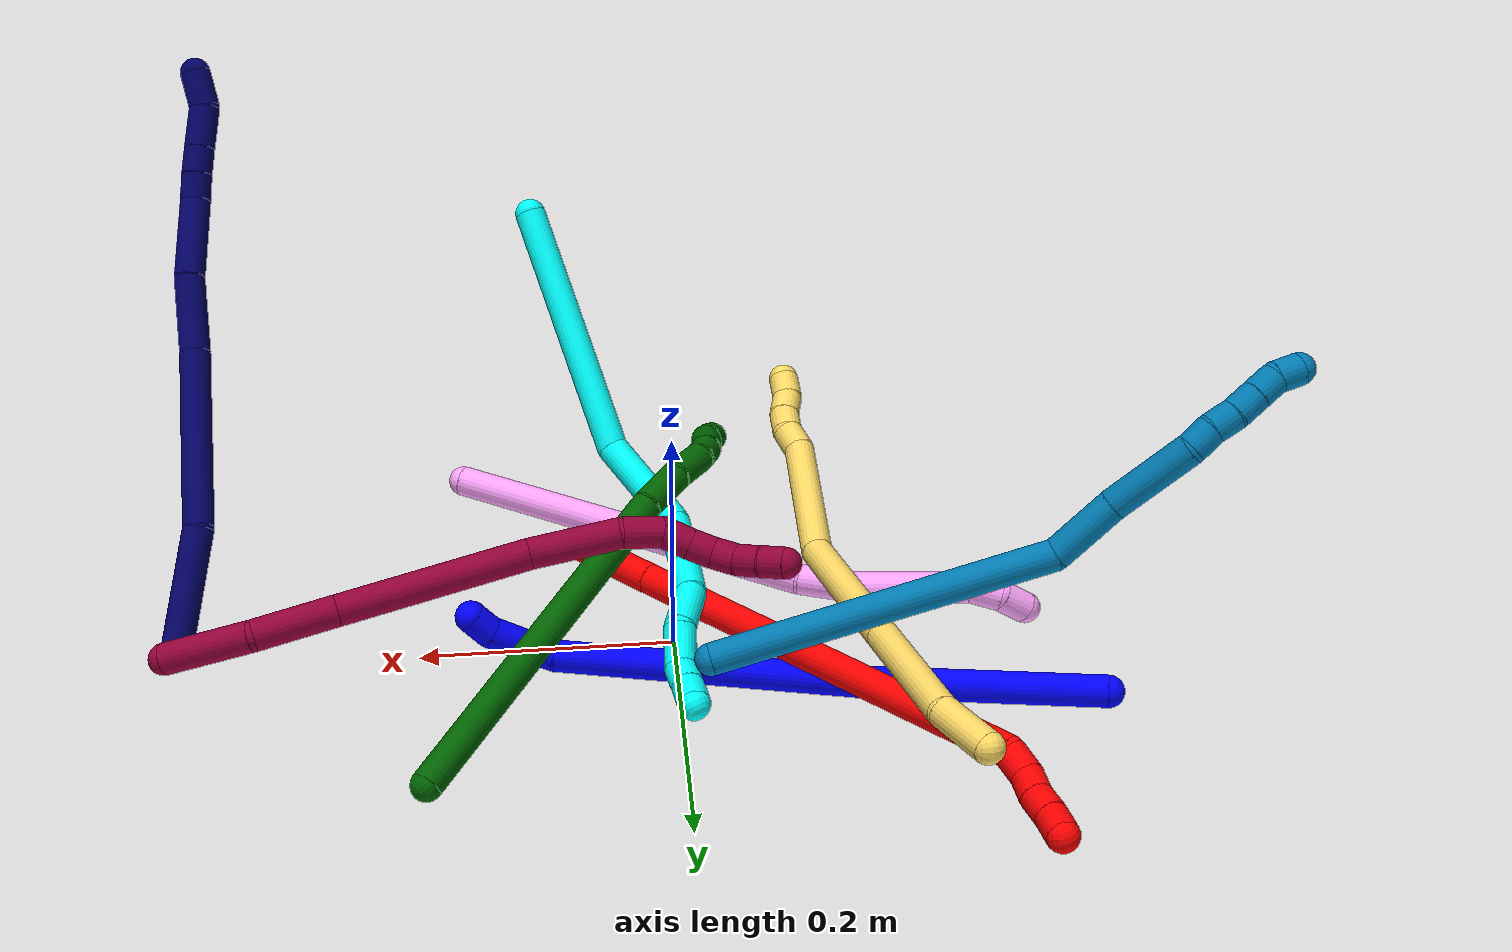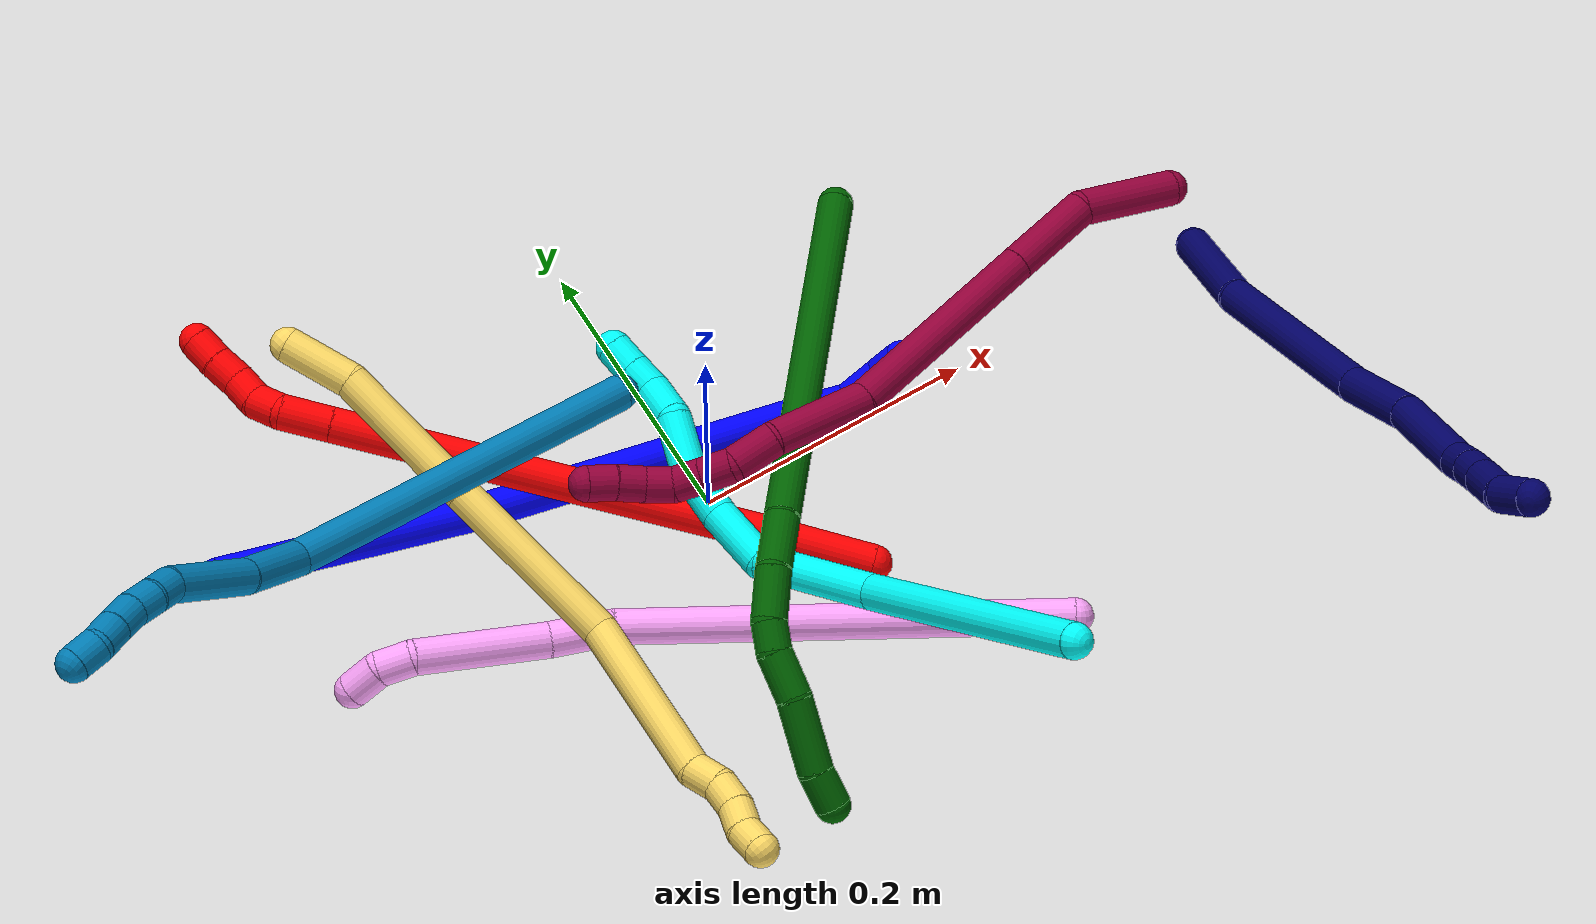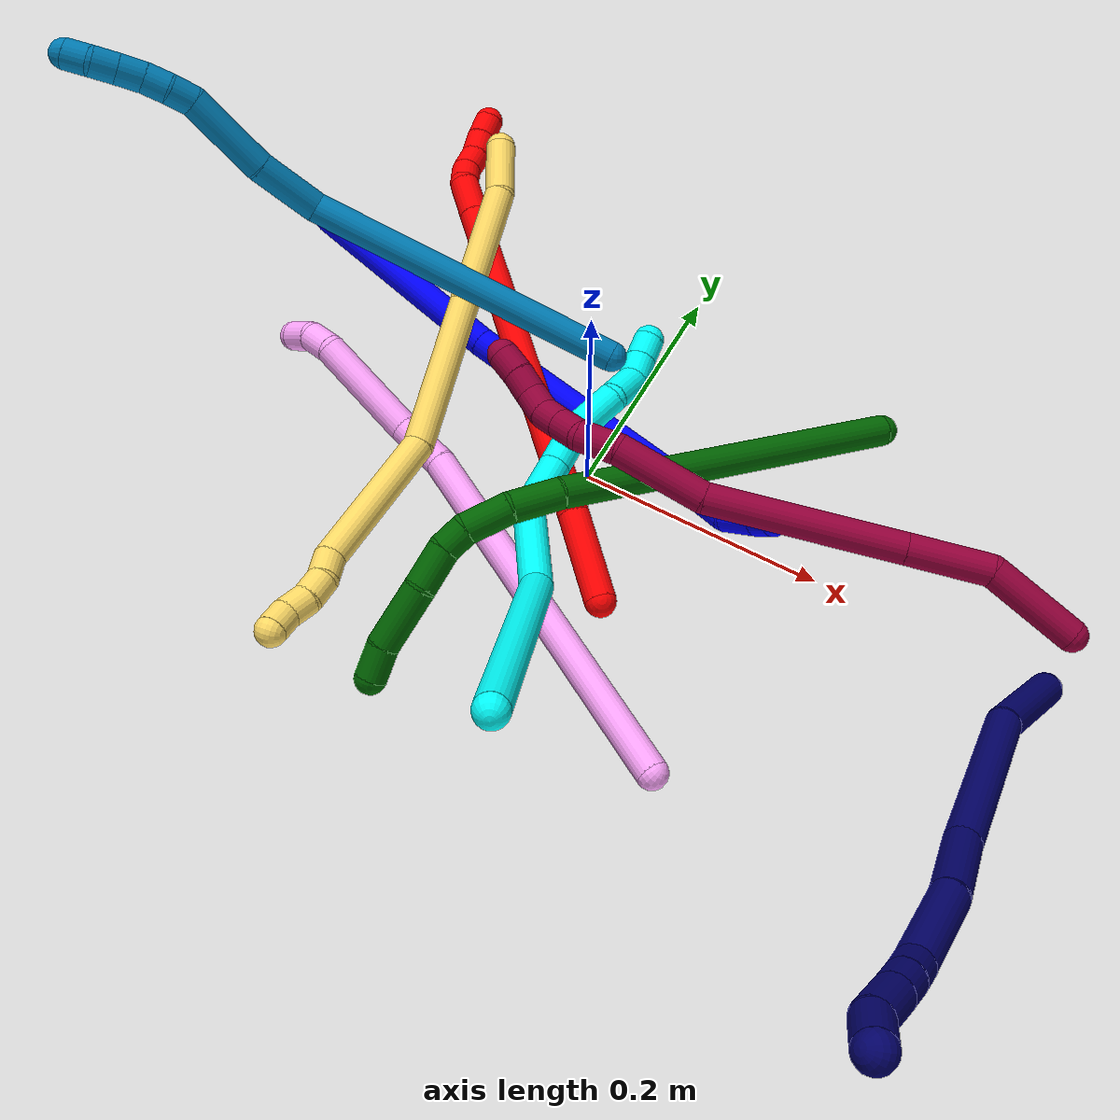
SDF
<sdf version="1.7">
 <world name="default">
  <plugin name="TubeGeneratorPlugin" filename="libtube_generator_plugin.so"/>
  <model name="photoneo_s_sensor">
   <static>1</static>
   <pose>0 0 2 1.57079 1.57079 3.14159</pose>
   <link name="link">
    <inertial><mass>0.1</mass></inertial>
    <sensor name="sensor" type="depth">
     <update_rate>30</update_rate>
     <camera>
      <horizontal_fov>1.22</horizontal_fov>
      <image><width>1920</width><height>1200</height><format>B8G8R8</format></image>
      <clip><near>0.1</near><far>4</far></clip>
      <depth_camera><output>points</output></depth_camera>
     </camera>
     <plugin name="camera_plugin" filename="libgazebo_ros_depth_camera.so">
      <baseline>0.2</baseline>
      <alwaysOn>1</alwaysOn>
      <updateRate>0.0</updateRate>
      <cameraName>camera_ir</cameraName>
      <imageTopicName>/camera/color/image_raw</imageTopicName>
      <cameraInfoTopicName>/camera/color/camera_info</cameraInfoTopicName>
      <depthImageTopicName>/camera/depth/image_raw</depthImageTopicName>
      <depthImageCameraInfoTopicName>/camera/depth/camera_info</depthImageCameraInfoTopicName>
      <pointCloudTopicName>/camera/depth/points</pointCloudTopicName>
      <frameName>fr_optical</frameName>
      <pointCloudCutoff>0.1</pointCloudCutoff>
      <pointCloudCutoffMax>2.0</pointCloudCutoffMax>
      <distortionK1>0</distortionK1>
      <distortionK2>0</distortionK2>
      <distortionK3>0</distortionK3>
      <distortionT1>0</distortionT1>
      <distortionT2>0</distortionT2>
      <CxPrime>0</CxPrime>
      <Cx>0</Cx>
      <Cy>0</Cy>
      <focalLength>0</focalLength>
      <hackBaseline>0</hackBaseline>
     </plugin>
    </sensor>
   </link>
  </model>
  <gravity>0 0 -9.8</gravity>
  <magnetic_field>6e-06 2.3e-05 -4.2e-05</magnetic_field>
  <atmosphere type="adiabatic"/>
  <physics name="default_physics" default="0" type="ode">
   <max_step_size>0.003</max_step_size>
   <real_time_factor>1</real_time_factor>
   <real_time_update_rate>1000</real_time_update_rate>
   <max_contacts>10000</max_contacts>
   <ode>
    <solver>
     <type>quick</type>
     <iters>100</iters>
     <sor>1.3</sor>
     <use_dynamic_moi_rescaling>0</use_dynamic_moi_rescaling>
    </solver>
    <constraints>
     <contact_max_correcting_vel>0</contact_max_correcting_vel>
     <contact_surface_layer>0.001</contact_surface_layer>
     <cfm>0</cfm>
     <erp>0.2</erp>
    </constraints>
   </ode>
  </physics>
  <scene><ambient>0.4 0.4 0.4 1</ambient><background>0.7 0.7 0.7 1</background><shadows>0</shadows></scene>
  <audio><device>default</device></audio>
  <spherical_coordinates>
   <surface_model>EARTH_WGS84</surface_model>
   <latitude_deg>0</latitude_deg>
   <longitude_deg>0</longitude_deg>
   <elevation>0</elevation>
   <heading_deg>0</heading_deg>
  </spherical_coordinates>
  <model name="bin">
   <static>1</static>
   <link name="bottom">
    <collision name="collision-bottom">
     <pose>0 0 -0.01 0 -0 0</pose>
     <geometry><box><size>0.8 0.6 0.02</size></box></geometry>
     <surface>
      <friction><ode><mu>100</mu><mu2>100</mu2></ode></friction>
      <contact><collide_bitmask>65535</collide_bitmask></contact>
     </surface>
    </collision>
   </link>
   <link name="west_wall">
    <collision name="collision-west_wall">
     <pose>-0.41 0 0.1 0 -0 0</pose>
     <geometry><box><size>0.02 0.6 0.2</size></box></geometry>
     <surface>
      <friction><ode><mu>100</mu><mu2>100</mu2></ode></friction>
      <contact><collide_bitmask>65535</collide_bitmask></contact>
     </surface>
    </collision>
   </link>
   <link name="east_wall">
    <collision name="collision-east_wall">
     <pose>0.41 0 0.1 0 -0 0</pose>
     <geometry><box><size>0.02 0.6 0.2</size></box></geometry>
     <surface>
      <friction><ode><mu>100</mu><mu2>100</mu2></ode></friction>
      <contact><collide_bitmask>65535</collide_bitmask></contact>
     </surface>
    </collision>
   </link>
   <link name="south_wall">
    <collision name="collision-south_wall">
     <pose>0 -0.31 0.1 0 -0 0</pose>
     <geometry><box><size>0.8 0.02 0.2</size></box></geometry>
     <surface>
      <friction><ode><mu>100</mu><mu2>100</mu2></ode></friction>
      <contact><collide_bitmask>65535</collide_bitmask></contact>
     </surface>
    </collision>
   </link>
   <link name="north_wall">
    <collision name="collision-north_wall">
     <pose>0 0.31 0.1 0 -0 0</pose>
     <geometry><box><size>0.8 0.02 0.2</size></box></geometry>
     <surface>
      <friction><ode><mu>100</mu><mu2>100</mu2></ode></friction>
      <contact><collide_bitmask>65535</collide_bitmask></contact>
     </surface>
    </collision>
   </link>
  </model>
  <model name="1">
   <static>0</static>
   <link name="1">
    <collision name="collision-cylinder-e_1_1_4">
     <pose>0.088569 -0.008068 0.028026 0.280296 1.2527 0.203439</pose>
     <geometry><cylinder><radius>0.0125</radius><length>0.186494</length></cylinder></geometry>
     <surface>
      <friction><ode><mu>1.16</mu><mu2>1.16</mu2><slip1>0</slip1><slip2>0</slip2></ode></friction>
      <contact><ode><kp>1e+06</kp><kd>1</kd><max_vel>0</max_vel><min_depth>0.001</min_depth></ode></contact>
     </surface>
    </collision>
    <visual name="visual-cylinder-e_1_1_4">
     <pose>0.088569 -0.008068 0.028026 0.280296 1.2527 0.203439</pose>
     <geometry><cylinder><radius>0.0125</radius><length>0.186494</length></cylinder></geometry>
     <material><ambient>0 0 1 1</ambient></material>
    </visual>
    <collision name="collision-cylinder-e_2_4_5">
     <pose>0.289374 -0.036433 0.089369 0.547164 1.23626 0.393917</pose>
     <geometry><cylinder><radius>0.0125</radius><length>0.237648</length></cylinder></geometry>
     <surface>
      <friction><ode><mu>1.16</mu><mu2>1.16</mu2><slip1>0</slip1><slip2>0</slip2></ode></friction>
      <contact><ode><kp>1e+06</kp><kd>1</kd><max_vel>0</max_vel><min_depth>0.001</min_depth></ode></contact>
     </surface>
    </collision>
    <visual name="visual-cylinder-e_2_4_5">
     <pose>0.289374 -0.036433 0.089369 0.547164 1.23626 0.393917</pose>
     <geometry><cylinder><radius>0.0125</radius><length>0.237648</length></cylinder></geometry>
     <material><ambient>0 0 1 1</ambient></material>
    </visual>
    <collision name="collision-cylinder-e_3_5_6">
     <pose>0.413946 -0.060266 0.123381 1.37671 1.2866 1.10517</pose>
     <geometry><cylinder><radius>0.0125</radius><length>0.025702</length></cylinder></geometry>
     <surface>
      <friction><ode><mu>1.16</mu><mu2>1.16</mu2><slip1>0</slip1><slip2>0</slip2></ode></friction>
      <contact><ode><kp>1e+06</kp><kd>1</kd><max_vel>0</max_vel><min_depth>0.001</min_depth></ode></contact>
     </surface>
    </collision>
    <visual name="visual-cylinder-e_3_5_6">
     <pose>0.413946 -0.060266 0.123381 1.37671 1.2866 1.10517</pose>
     <geometry><cylinder><radius>0.0125</radius><length>0.025702</length></cylinder></geometry>
     <material><ambient>0 0 1 1</ambient></material>
    </visual>
    <collision name="collision-cylinder-e_4_6_7">
     <pose>0.437367 -0.073614 0.126085 1.36886 0.83606 0.695502</pose>
     <geometry><cylinder><radius>0.0125</radius><length>0.02988</length></cylinder></geometry>
     <surface>
      <friction><ode><mu>1.16</mu><mu2>1.16</mu2><slip1>0</slip1><slip2>0</slip2></ode></friction>
      <contact><ode><kp>1e+06</kp><kd>1</kd><max_vel>0</max_vel><min_depth>0.001</min_depth></ode></contact>
     </surface>
    </collision>
    <visual name="visual-cylinder-e_4_6_7">
     <pose>0.437367 -0.073614 0.126085 1.36886 0.83606 0.695502</pose>
     <geometry><cylinder><radius>0.0125</radius><length>0.02988</length></cylinder></geometry>
     <material><ambient>0 0 1 1</ambient></material>
    </visual>
    <collision name="collision-cylinder-e_5_7_2">
     <pose>0.455026 -0.091016 0.126694 1.75317 0.70545 0.832726</pose>
     <geometry><cylinder><radius>0.0125</radius><length>0.020277</length></cylinder></geometry>
     <surface>
      <friction><ode><mu>1.16</mu><mu2>1.16</mu2><slip1>0</slip1><slip2>0</slip2></ode></friction>
      <contact><ode><kp>1e+06</kp><kd>1</kd><max_vel>0</max_vel><min_depth>0.001</min_depth></ode></contact>
     </surface>
    </collision>
    <visual name="visual-cylinder-e_5_7_2">
     <pose>0.455026 -0.091016 0.126694 1.75317 0.70545 0.832726</pose>
     <geometry><cylinder><radius>0.0125</radius><length>0.020277</length></cylinder></geometry>
     <material><ambient>0 0 1 1</ambient></material>
    </visual>
    <collision name="collision-sphere-2">
     <pose>0.4616 -0.098607 0.125294 0 -0 0</pose>
     <geometry><sphere><radius>0.0125</radius></sphere></geometry>
     <surface>
      <friction><ode><mu>1.16</mu><mu2>1.16</mu2><slip1>0</slip1><slip2>0</slip2></ode></friction>
      <contact><ode><kp>1e+06</kp><kd>1</kd><max_vel>0</max_vel><min_depth>0.001</min_depth></ode></contact>
     </surface>
    </collision>
    <visual name="visual-sphere-2">
     <pose>0.4616 -0.098607 0.125294 0 -0 0</pose>
     <geometry><sphere><radius>0.0125</radius></sphere></geometry>
     <material><ambient>0 0 1 1</ambient></material>
    </visual>
    <collision name="collision-sphere-7">
     <pose>0.448453 -0.083426 0.128094 0 -0 0</pose>
     <geometry><sphere><radius>0.0125</radius></sphere></geometry>
     <surface>
      <friction><ode><mu>1.16</mu><mu2>1.16</mu2><slip1>0</slip1><slip2>0</slip2></ode></friction>
      <contact><ode><kp>1e+06</kp><kd>1</kd><max_vel>0</max_vel><min_depth>0.001</min_depth></ode></contact>
     </surface>
    </collision>
    <visual name="visual-sphere-7">
     <pose>0.448453 -0.083426 0.128094 0 -0 0</pose>
     <geometry><sphere><radius>0.0125</radius></sphere></geometry>
     <material><ambient>0 0 1 1</ambient></material>
    </visual>
    <collision name="collision-sphere-6">
     <pose>0.426282 -0.063801 0.124076 0 -0 0</pose>
     <geometry><sphere><radius>0.0125</radius></sphere></geometry>
     <surface>
      <friction><ode><mu>1.16</mu><mu2>1.16</mu2><slip1>0</slip1><slip2>0</slip2></ode></friction>
      <contact><ode><kp>1e+06</kp><kd>1</kd><max_vel>0</max_vel><min_depth>0.001</min_depth></ode></contact>
     </surface>
    </collision>
    <visual name="visual-sphere-6">
     <pose>0.426282 -0.063801 0.124076 0 -0 0</pose>
     <geometry><sphere><radius>0.0125</radius></sphere></geometry>
     <material><ambient>0 0 1 1</ambient></material>
    </visual>
    <collision name="collision-sphere-5">
     <pose>0.401611 -0.05673 0.122686 0 -0 0</pose>
     <geometry><sphere><radius>0.0125</radius></sphere></geometry>
     <surface>
      <friction><ode><mu>1.16</mu><mu2>1.16</mu2><slip1>0</slip1><slip2>0</slip2></ode></friction>
      <contact><ode><kp>1e+06</kp><kd>1</kd><max_vel>0</max_vel><min_depth>0.001</min_depth></ode></contact>
     </surface>
    </collision>
    <visual name="visual-sphere-5">
     <pose>0.401611 -0.05673 0.122686 0 -0 0</pose>
     <geometry><sphere><radius>0.0125</radius></sphere></geometry>
     <material><ambient>0 0 1 1</ambient></material>
    </visual>
    <collision name="collision-sphere-1">
     <geometry><sphere><radius>0.0125</radius></sphere></geometry>
     <surface>
      <friction><ode><mu>1.16</mu><mu2>1.16</mu2><slip1>0</slip1><slip2>0</slip2></ode></friction>
      <contact><ode><kp>1e+06</kp><kd>1</kd><max_vel>0</max_vel><min_depth>0.001</min_depth></ode></contact>
     </surface>
    </collision>
    <visual name="visual-sphere-1">
     <geometry><sphere><radius>0.0125</radius></sphere></geometry>
     <material><ambient>0 0 1 1</ambient></material>
    </visual>
    <collision name="collision-sphere-4">
     <pose>0.177138 -0.016136 0.056051 0 -0 0</pose>
     <geometry><sphere><radius>0.0125</radius></sphere></geometry>
     <surface>
      <friction><ode><mu>1.16</mu><mu2>1.16</mu2><slip1>0</slip1><slip2>0</slip2></ode></friction>
      <contact><ode><kp>1e+06</kp><kd>1</kd><max_vel>0</max_vel><min_depth>0.001</min_depth></ode></contact>
     </surface>
    </collision>
    <visual name="visual-sphere-4">
     <pose>0.177138 -0.016136 0.056051 0 -0 0</pose>
     <geometry><sphere><radius>0.0125</radius></sphere></geometry>
     <material><ambient>0 0 1 1</ambient></material>
    </visual>
    <inertial>
     <pose>0.236442 -0.031514 0.071945 0 -0 0</pose>
     <mass>0.5</mass>
     <inertia>
      <ixx>0.000728</ixx>
      <ixy>0</ixy>
      <ixz>0</ixz>
      <iyy>0.001823</iyy>
      <iyz>0</iyz>
      <izz>-0.001338</izz>
     </inertia>
    </inertial>
   </link>
   <pose>-0.319494 0.111926 0.027124 -2.06381 0.018772 -0.545442</pose>
  </model>
  <model name="2">
   <static>0</static>
   <link name="2">
    <collision name="collision-cylinder-e_1_1_4">
     <pose>-0.014885 0.032686 0.012403 -1.20812 -0.402538 0.279772</pose>
     <geometry><cylinder><radius>0.0125</radius><length>0.075994</length></cylinder></geometry>
     <surface>
      <friction><ode><mu>1.16</mu><mu2>1.16</mu2><slip1>0</slip1><slip2>0</slip2></ode></friction>
      <contact><ode><kp>1e+06</kp><kd>1</kd><max_vel>0</max_vel><min_depth>0.001</min_depth></ode></contact>
     </surface>
    </collision>
    <visual name="visual-cylinder-e_1_1_4">
     <pose>-0.014885 0.032686 0.012403 -1.20812 -0.402538 0.279772</pose>
     <geometry><cylinder><radius>0.0125</radius><length>0.075994</length></cylinder></geometry>
     <material><ambient>1 0 0 1</ambient></material>
    </visual>
    <collision name="collision-cylinder-e_2_4_5">
     <pose>-0.086774 0.196904 0.076241 -1.19803 -0.38362 0.263617</pose>
     <geometry><cylinder><radius>0.0125</radius><length>0.304603</length></cylinder></geometry>
     <surface>
      <friction><ode><mu>1.16</mu><mu2>1.16</mu2><slip1>0</slip1><slip2>0</slip2></ode></friction>
      <contact><ode><kp>1e+06</kp><kd>1</kd><max_vel>0</max_vel><min_depth>0.001</min_depth></ode></contact>
     </surface>
    </collision>
    <visual name="visual-cylinder-e_2_4_5">
     <pose>-0.086774 0.196904 0.076241 -1.19803 -0.38362 0.263617</pose>
     <geometry><cylinder><radius>0.0125</radius><length>0.304603</length></cylinder></geometry>
     <material><ambient>1 0 0 1</ambient></material>
    </visual>
    <collision name="collision-cylinder-e_3_5_6">
     <pose>-0.1506 0.34389 0.133885 -1.1888 -0.388765 0.264591</pose>
     <geometry><cylinder><radius>0.0125</radius><length>0.035995</length></cylinder></geometry>
     <surface>
      <friction><ode><mu>1.16</mu><mu2>1.16</mu2><slip1>0</slip1><slip2>0</slip2></ode></friction>
      <contact><ode><kp>1e+06</kp><kd>1</kd><max_vel>0</max_vel><min_depth>0.001</min_depth></ode></contact>
     </surface>
    </collision>
    <visual name="visual-cylinder-e_3_5_6">
     <pose>-0.1506 0.34389 0.133885 -1.1888 -0.388765 0.264591</pose>
     <geometry><cylinder><radius>0.0125</radius><length>0.035995</length></cylinder></geometry>
     <material><ambient>1 0 0 1</ambient></material>
    </visual>
    <collision name="collision-cylinder-e_4_6_7">
     <pose>-0.16351 0.365348 0.146732 -0.735179 -0.597365 0.236033</pose>
     <geometry><cylinder><radius>0.0125</radius><length>0.02165</length></cylinder></geometry>
     <surface>
      <friction><ode><mu>1.16</mu><mu2>1.16</mu2><slip1>0</slip1><slip2>0</slip2></ode></friction>
      <contact><ode><kp>1e+06</kp><kd>1</kd><max_vel>0</max_vel><min_depth>0.001</min_depth></ode></contact>
     </surface>
    </collision>
    <visual name="visual-cylinder-e_4_6_7">
     <pose>-0.16351 0.365348 0.146732 -0.735179 -0.597365 0.236033</pose>
     <geometry><cylinder><radius>0.0125</radius><length>0.02165</length></cylinder></geometry>
     <material><ambient>1 0 0 1</ambient></material>
    </visual>
    <collision name="collision-cylinder-e_5_7_8">
     <pose>-0.17803 0.375352 0.157298 -0.794622 -0.983954 0.442422</pose>
     <geometry><cylinder><radius>0.0125</radius><length>0.020251</length></cylinder></geometry>
     <surface>
      <friction><ode><mu>1.16</mu><mu2>1.16</mu2><slip1>0</slip1><slip2>0</slip2></ode></friction>
      <contact><ode><kp>1e+06</kp><kd>1</kd><max_vel>0</max_vel><min_depth>0.001</min_depth></ode></contact>
     </surface>
    </collision>
    <visual name="visual-cylinder-e_5_7_8">
     <pose>-0.17803 0.375352 0.157298 -0.794622 -0.983954 0.442422</pose>
     <geometry><cylinder><radius>0.0125</radius><length>0.020251</length></cylinder></geometry>
     <material><ambient>1 0 0 1</ambient></material>
    </visual>
    <collision name="collision-cylinder-e_6_8_9">
     <pose>-0.194522 0.385255 0.164403 -1.07697 -0.877053 0.546307</pose>
     <geometry><cylinder><radius>0.0125</radius><length>0.020966</length></cylinder></geometry>
     <surface>
      <friction><ode><mu>1.16</mu><mu2>1.16</mu2><slip1>0</slip1><slip2>0</slip2></ode></friction>
      <contact><ode><kp>1e+06</kp><kd>1</kd><max_vel>0</max_vel><min_depth>0.001</min_depth></ode></contact>
     </surface>
    </collision>
    <visual name="visual-cylinder-e_6_8_9">
     <pose>-0.194522 0.385255 0.164403 -1.07697 -0.877053 0.546307</pose>
     <geometry><cylinder><radius>0.0125</radius><length>0.020966</length></cylinder></geometry>
     <material><ambient>1 0 0 1</ambient></material>
    </visual>
    <collision name="collision-cylinder-e_7_9_2">
     <pose>-0.211078 0.396095 0.170568 -1.0266 -0.974152 0.580267</pose>
     <geometry><cylinder><radius>0.0125</radius><length>0.020541</length></cylinder></geometry>
     <surface>
      <friction><ode><mu>1.16</mu><mu2>1.16</mu2><slip1>0</slip1><slip2>0</slip2></ode></friction>
      <contact><ode><kp>1e+06</kp><kd>1</kd><max_vel>0</max_vel><min_depth>0.001</min_depth></ode></contact>
     </surface>
    </collision>
    <visual name="visual-cylinder-e_7_9_2">
     <pose>-0.211078 0.396095 0.170568 -1.0266 -0.974152 0.580267</pose>
     <geometry><cylinder><radius>0.0125</radius><length>0.020541</length></cylinder></geometry>
     <material><ambient>1 0 0 1</ambient></material>
    </visual>
    <collision name="collision-sphere-2">
     <pose>-0.219574 0.401032 0.173556 0 -0 0</pose>
     <geometry><sphere><radius>0.0125</radius></sphere></geometry>
     <surface>
      <friction><ode><mu>1.16</mu><mu2>1.16</mu2><slip1>0</slip1><slip2>0</slip2></ode></friction>
      <contact><ode><kp>1e+06</kp><kd>1</kd><max_vel>0</max_vel><min_depth>0.001</min_depth></ode></contact>
     </surface>
    </collision>
    <visual name="visual-sphere-2">
     <pose>-0.219574 0.401032 0.173556 0 -0 0</pose>
     <geometry><sphere><radius>0.0125</radius></sphere></geometry>
     <material><ambient>1 0 0 1</ambient></material>
    </visual>
    <collision name="collision-sphere-9">
     <pose>-0.202582 0.391157 0.16758 0 -0 0</pose>
     <geometry><sphere><radius>0.0125</radius></sphere></geometry>
     <surface>
      <friction><ode><mu>1.16</mu><mu2>1.16</mu2><slip1>0</slip1><slip2>0</slip2></ode></friction>
      <contact><ode><kp>1e+06</kp><kd>1</kd><max_vel>0</max_vel><min_depth>0.001</min_depth></ode></contact>
     </surface>
    </collision>
    <visual name="visual-sphere-9">
     <pose>-0.202582 0.391157 0.16758 0 -0 0</pose>
     <geometry><sphere><radius>0.0125</radius></sphere></geometry>
     <material><ambient>1 0 0 1</ambient></material>
    </visual>
    <collision name="collision-sphere-4">
     <pose>-0.029771 0.065371 0.024806 0 -0 0</pose>
     <geometry><sphere><radius>0.0125</radius></sphere></geometry>
     <surface>
      <friction><ode><mu>1.16</mu><mu2>1.16</mu2><slip1>0</slip1><slip2>0</slip2></ode></friction>
      <contact><ode><kp>1e+06</kp><kd>1</kd><max_vel>0</max_vel><min_depth>0.001</min_depth></ode></contact>
     </surface>
    </collision>
    <visual name="visual-sphere-4">
     <pose>-0.029771 0.065371 0.024806 0 -0 0</pose>
     <geometry><sphere><radius>0.0125</radius></sphere></geometry>
     <material><ambient>1 0 0 1</ambient></material>
    </visual>
    <collision name="collision-sphere-1">
     <geometry><sphere><radius>0.0125</radius></sphere></geometry>
     <surface>
      <friction><ode><mu>1.16</mu><mu2>1.16</mu2><slip1>0</slip1><slip2>0</slip2></ode></friction>
      <contact><ode><kp>1e+06</kp><kd>1</kd><max_vel>0</max_vel><min_depth>0.001</min_depth></ode></contact>
     </surface>
    </collision>
    <visual name="visual-sphere-1">
     <geometry><sphere><radius>0.0125</radius></sphere></geometry>
     <material><ambient>1 0 0 1</ambient></material>
    </visual>
    <collision name="collision-sphere-8">
     <pose>-0.186462 0.379353 0.161226 0 -0 0</pose>
     <geometry><sphere><radius>0.0125</radius></sphere></geometry>
     <surface>
      <friction><ode><mu>1.16</mu><mu2>1.16</mu2><slip1>0</slip1><slip2>0</slip2></ode></friction>
      <contact><ode><kp>1e+06</kp><kd>1</kd><max_vel>0</max_vel><min_depth>0.001</min_depth></ode></contact>
     </surface>
    </collision>
    <visual name="visual-sphere-8">
     <pose>-0.186462 0.379353 0.161226 0 -0 0</pose>
     <geometry><sphere><radius>0.0125</radius></sphere></geometry>
     <material><ambient>1 0 0 1</ambient></material>
    </visual>
    <collision name="collision-sphere-5">
     <pose>-0.143778 0.328436 0.127676 0 -0 0</pose>
     <geometry><sphere><radius>0.0125</radius></sphere></geometry>
     <surface>
      <friction><ode><mu>1.16</mu><mu2>1.16</mu2><slip1>0</slip1><slip2>0</slip2></ode></friction>
      <contact><ode><kp>1e+06</kp><kd>1</kd><max_vel>0</max_vel><min_depth>0.001</min_depth></ode></contact>
     </surface>
    </collision>
    <visual name="visual-sphere-5">
     <pose>-0.143778 0.328436 0.127676 0 -0 0</pose>
     <geometry><sphere><radius>0.0125</radius></sphere></geometry>
     <material><ambient>1 0 0 1</ambient></material>
    </visual>
    <collision name="collision-sphere-6">
     <pose>-0.157422 0.359345 0.140093 0 -0 0</pose>
     <geometry><sphere><radius>0.0125</radius></sphere></geometry>
     <surface>
      <friction><ode><mu>1.16</mu><mu2>1.16</mu2><slip1>0</slip1><slip2>0</slip2></ode></friction>
      <contact><ode><kp>1e+06</kp><kd>1</kd><max_vel>0</max_vel><min_depth>0.001</min_depth></ode></contact>
     </surface>
    </collision>
    <visual name="visual-sphere-6">
     <pose>-0.157422 0.359345 0.140093 0 -0 0</pose>
     <geometry><sphere><radius>0.0125</radius></sphere></geometry>
     <material><ambient>1 0 0 1</ambient></material>
    </visual>
    <collision name="collision-sphere-7">
     <pose>-0.169599 0.371351 0.15337 0 -0 0</pose>
     <geometry><sphere><radius>0.0125</radius></sphere></geometry>
     <surface>
      <friction><ode><mu>1.16</mu><mu2>1.16</mu2><slip1>0</slip1><slip2>0</slip2></ode></friction>
      <contact><ode><kp>1e+06</kp><kd>1</kd><max_vel>0</max_vel><min_depth>0.001</min_depth></ode></contact>
     </surface>
    </collision>
    <visual name="visual-sphere-7">
     <pose>-0.169599 0.371351 0.15337 0 -0 0</pose>
     <geometry><sphere><radius>0.0125</radius></sphere></geometry>
     <material><ambient>1 0 0 1</ambient></material>
    </visual>
    <inertial>
     <pose>-0.097086 0.213129 0.084595 0 -0 0</pose>
     <mass>0.5</mass>
     <inertia>
      <ixx>0.00273</ixx>
      <ixy>0</ixy>
      <ixz>0</ixz>
      <iyy>0.001689</iyy>
      <iyz>0</iyz>
      <izz>-0.001164</izz>
     </inertia>
    </inertial>
   </link>
   <pose>0.068073 -0.104829 0.017121 2.76774 0.199733 -1.97361</pose>
  </model>
  <model name="3">
   <static>0</static>
   <link name="3">
    <collision name="collision-cylinder-e_1_1_4">
     <pose>0.018378 -0.004566 -0.103987 3.09771 0.174766 2.65075</pose>
     <geometry><cylinder><radius>0.0125</radius><length>0.211395</length></cylinder></geometry>
     <surface>
      <friction><ode><mu>1.16</mu><mu2>1.16</mu2><slip1>0</slip1><slip2>0</slip2></ode></friction>
      <contact><ode><kp>1e+06</kp><kd>1</kd><max_vel>0</max_vel><min_depth>0.001</min_depth></ode></contact>
     </surface>
    </collision>
    <visual name="visual-cylinder-e_1_1_4">
     <pose>0.018378 -0.004566 -0.103987 3.09771 0.174766 2.65075</pose>
     <geometry><cylinder><radius>0.0125</radius><length>0.211395</length></cylinder></geometry>
     <material><ambient>0.003922 1 0.996078 1</ambient></material>
    </visual>
    <collision name="collision-cylinder-e_2_4_5">
     <pose>0.025772 -0.007312 -0.249645 -3.09795 -0.257524 2.80757</pose>
     <geometry><cylinder><radius>0.0125</radius><length>0.086264</length></cylinder></geometry>
     <surface>
      <friction><ode><mu>1.16</mu><mu2>1.16</mu2><slip1>0</slip1><slip2>0</slip2></ode></friction>
      <contact><ode><kp>1e+06</kp><kd>1</kd><max_vel>0</max_vel><min_depth>0.001</min_depth></ode></contact>
     </surface>
    </collision>
    <visual name="visual-cylinder-e_2_4_5">
     <pose>0.025772 -0.007312 -0.249645 -3.09795 -0.257524 2.80757</pose>
     <geometry><cylinder><radius>0.0125</radius><length>0.086264</length></cylinder></geometry>
     <material><ambient>0.003922 1 0.996078 1</ambient></material>
    </visual>
    <collision name="collision-cylinder-e_3_5_6">
     <pose>0.013323 0.006406 -0.312446 -2.62883 -0.060268 0.228964</pose>
     <geometry><cylinder><radius>0.0125</radius><length>0.04859</length></cylinder></geometry>
     <surface>
      <friction><ode><mu>1.16</mu><mu2>1.16</mu2><slip1>0</slip1><slip2>0</slip2></ode></friction>
      <contact><ode><kp>1e+06</kp><kd>1</kd><max_vel>0</max_vel><min_depth>0.001</min_depth></ode></contact>
     </surface>
    </collision>
    <visual name="visual-cylinder-e_3_5_6">
     <pose>0.013323 0.006406 -0.312446 -2.62883 -0.060268 0.228964</pose>
     <geometry><cylinder><radius>0.0125</radius><length>0.04859</length></cylinder></geometry>
     <material><ambient>0.003922 1 0.996078 1</ambient></material>
    </visual>
    <collision name="collision-cylinder-e_4_6_7">
     <pose>0.008764 0.029755 -0.346906 -2.43171 -0.174397 0.463263</pose>
     <geometry><cylinder><radius>0.0125</radius><length>0.035686</length></cylinder></geometry>
     <surface>
      <friction><ode><mu>1.16</mu><mu2>1.16</mu2><slip1>0</slip1><slip2>0</slip2></ode></friction>
      <contact><ode><kp>1e+06</kp><kd>1</kd><max_vel>0</max_vel><min_depth>0.001</min_depth></ode></contact>
     </surface>
    </collision>
    <visual name="visual-cylinder-e_4_6_7">
     <pose>0.008764 0.029755 -0.346906 -2.43171 -0.174397 0.463263</pose>
     <geometry><cylinder><radius>0.0125</radius><length>0.035686</length></cylinder></geometry>
     <material><ambient>0.003922 1 0.996078 1</ambient></material>
    </visual>
    <collision name="collision-cylinder-e_5_7_8">
     <pose>0.007353 0.057984 -0.373338 -2.23394 0.078978 -0.161644</pose>
     <geometry><cylinder><radius>0.0125</radius><length>0.042708</length></cylinder></geometry>
     <surface>
      <friction><ode><mu>1.16</mu><mu2>1.16</mu2><slip1>0</slip1><slip2>0</slip2></ode></friction>
      <contact><ode><kp>1e+06</kp><kd>1</kd><max_vel>0</max_vel><min_depth>0.001</min_depth></ode></contact>
     </surface>
    </collision>
    <visual name="visual-cylinder-e_5_7_8">
     <pose>0.007353 0.057984 -0.373338 -2.23394 0.078978 -0.161644</pose>
     <geometry><cylinder><radius>0.0125</radius><length>0.042708</length></cylinder></geometry>
     <material><ambient>0.003922 1 0.996078 1</ambient></material>
    </visual>
    <collision name="collision-cylinder-e_6_8_9">
     <pose>0.012637 0.081865 -0.401336 -2.69642 0.214783 -0.889038</pose>
     <geometry><cylinder><radius>0.0125</radius><length>0.03378</length></cylinder></geometry>
     <surface>
      <friction><ode><mu>1.16</mu><mu2>1.16</mu2><slip1>0</slip1><slip2>0</slip2></ode></friction>
      <contact><ode><kp>1e+06</kp><kd>1</kd><max_vel>0</max_vel><min_depth>0.001</min_depth></ode></contact>
     </surface>
    </collision>
    <visual name="visual-cylinder-e_6_8_9">
     <pose>0.012637 0.081865 -0.401336 -2.69642 0.214783 -0.889038</pose>
     <geometry><cylinder><radius>0.0125</radius><length>0.03378</length></cylinder></geometry>
     <material><ambient>0.003922 1 0.996078 1</ambient></material>
    </visual>
    <collision name="collision-cylinder-e_7_9_10">
     <pose>0.01362 0.094557 -0.424611 -2.55372 -0.254288 0.799176</pose>
     <geometry><cylinder><radius>0.0125</radius><length>0.020812</length></cylinder></geometry>
     <surface>
      <friction><ode><mu>1.16</mu><mu2>1.16</mu2><slip1>0</slip1><slip2>0</slip2></ode></friction>
      <contact><ode><kp>1e+06</kp><kd>1</kd><max_vel>0</max_vel><min_depth>0.001</min_depth></ode></contact>
     </surface>
    </collision>
    <visual name="visual-cylinder-e_7_9_10">
     <pose>0.01362 0.094557 -0.424611 -2.55372 -0.254288 0.799176</pose>
     <geometry><cylinder><radius>0.0125</radius><length>0.020812</length></cylinder></geometry>
     <material><ambient>0.003922 1 0.996078 1</ambient></material>
    </visual>
    <collision name="collision-cylinder-e_8_10_2">
     <pose>0.008661 0.106015 -0.441227 -2.52216 -0.227385 0.685458</pose>
     <geometry><cylinder><radius>0.0125</radius><length>0.020765</length></cylinder></geometry>
     <surface>
      <friction><ode><mu>1.16</mu><mu2>1.16</mu2><slip1>0</slip1><slip2>0</slip2></ode></friction>
      <contact><ode><kp>1e+06</kp><kd>1</kd><max_vel>0</max_vel><min_depth>0.001</min_depth></ode></contact>
     </surface>
    </collision>
    <visual name="visual-cylinder-e_8_10_2">
     <pose>0.008661 0.106015 -0.441227 -2.52216 -0.227385 0.685458</pose>
     <geometry><cylinder><radius>0.0125</radius><length>0.020765</length></cylinder></geometry>
     <material><ambient>0.003922 1 0.996078 1</ambient></material>
    </visual>
    <collision name="collision-sphere-2">
     <pose>0.006321 0.111887 -0.449463 0 -0 0</pose>
     <geometry><sphere><radius>0.0125</radius></sphere></geometry>
     <surface>
      <friction><ode><mu>1.16</mu><mu2>1.16</mu2><slip1>0</slip1><slip2>0</slip2></ode></friction>
      <contact><ode><kp>1e+06</kp><kd>1</kd><max_vel>0</max_vel><min_depth>0.001</min_depth></ode></contact>
     </surface>
    </collision>
    <visual name="visual-sphere-2">
     <pose>0.006321 0.111887 -0.449463 0 -0 0</pose>
     <geometry><sphere><radius>0.0125</radius></sphere></geometry>
     <material><ambient>0.003922 1 0.996078 1</ambient></material>
    </visual>
    <collision name="collision-sphere-10">
     <pose>0.011002 0.100142 -0.432991 0 -0 0</pose>
     <geometry><sphere><radius>0.0125</radius></sphere></geometry>
     <surface>
      <friction><ode><mu>1.16</mu><mu2>1.16</mu2><slip1>0</slip1><slip2>0</slip2></ode></friction>
      <contact><ode><kp>1e+06</kp><kd>1</kd><max_vel>0</max_vel><min_depth>0.001</min_depth></ode></contact>
     </surface>
    </collision>
    <visual name="visual-sphere-10">
     <pose>0.011002 0.100142 -0.432991 0 -0 0</pose>
     <geometry><sphere><radius>0.0125</radius></sphere></geometry>
     <material><ambient>0.003922 1 0.996078 1</ambient></material>
    </visual>
    <collision name="collision-sphere-9">
     <pose>0.016237 0.088971 -0.41623 0 -0 0</pose>
     <geometry><sphere><radius>0.0125</radius></sphere></geometry>
     <surface>
      <friction><ode><mu>1.16</mu><mu2>1.16</mu2><slip1>0</slip1><slip2>0</slip2></ode></friction>
      <contact><ode><kp>1e+06</kp><kd>1</kd><max_vel>0</max_vel><min_depth>0.001</min_depth></ode></contact>
     </surface>
    </collision>
    <visual name="visual-sphere-9">
     <pose>0.016237 0.088971 -0.41623 0 -0 0</pose>
     <geometry><sphere><radius>0.0125</radius></sphere></geometry>
     <material><ambient>0.003922 1 0.996078 1</ambient></material>
    </visual>
    <collision name="collision-sphere-4">
     <pose>0.036757 -0.009132 -0.207975 0 -0 0</pose>
     <geometry><sphere><radius>0.0125</radius></sphere></geometry>
     <surface>
      <friction><ode><mu>1.16</mu><mu2>1.16</mu2><slip1>0</slip1><slip2>0</slip2></ode></friction>
      <contact><ode><kp>1e+06</kp><kd>1</kd><max_vel>0</max_vel><min_depth>0.001</min_depth></ode></contact>
     </surface>
    </collision>
    <visual name="visual-sphere-4">
     <pose>0.036757 -0.009132 -0.207975 0 -0 0</pose>
     <geometry><sphere><radius>0.0125</radius></sphere></geometry>
     <material><ambient>0.003922 1 0.996078 1</ambient></material>
    </visual>
    <collision name="collision-sphere-1">
     <geometry><sphere><radius>0.0125</radius></sphere></geometry>
     <surface>
      <friction><ode><mu>1.16</mu><mu2>1.16</mu2><slip1>0</slip1><slip2>0</slip2></ode></friction>
      <contact><ode><kp>1e+06</kp><kd>1</kd><max_vel>0</max_vel><min_depth>0.001</min_depth></ode></contact>
     </surface>
    </collision>
    <visual name="visual-sphere-1">
     <geometry><sphere><radius>0.0125</radius></sphere></geometry>
     <material><ambient>0.003922 1 0.996078 1</ambient></material>
    </visual>
    <collision name="collision-sphere-8">
     <pose>0.009038 0.074759 -0.386443 0 -0 0</pose>
     <geometry><sphere><radius>0.0125</radius></sphere></geometry>
     <surface>
      <friction><ode><mu>1.16</mu><mu2>1.16</mu2><slip1>0</slip1><slip2>0</slip2></ode></friction>
      <contact><ode><kp>1e+06</kp><kd>1</kd><max_vel>0</max_vel><min_depth>0.001</min_depth></ode></contact>
     </surface>
    </collision>
    <visual name="visual-sphere-8">
     <pose>0.009038 0.074759 -0.386443 0 -0 0</pose>
     <geometry><sphere><radius>0.0125</radius></sphere></geometry>
     <material><ambient>0.003922 1 0.996078 1</ambient></material>
    </visual>
    <collision name="collision-sphere-5">
     <pose>0.014787 -0.005492 -0.291314 0 -0 0</pose>
     <geometry><sphere><radius>0.0125</radius></sphere></geometry>
     <surface>
      <friction><ode><mu>1.16</mu><mu2>1.16</mu2><slip1>0</slip1><slip2>0</slip2></ode></friction>
      <contact><ode><kp>1e+06</kp><kd>1</kd><max_vel>0</max_vel><min_depth>0.001</min_depth></ode></contact>
     </surface>
    </collision>
    <visual name="visual-sphere-5">
     <pose>0.014787 -0.005492 -0.291314 0 -0 0</pose>
     <geometry><sphere><radius>0.0125</radius></sphere></geometry>
     <material><ambient>0.003922 1 0.996078 1</ambient></material>
    </visual>
    <collision name="collision-sphere-6">
     <pose>0.01186 0.018303 -0.333579 0 -0 0</pose>
     <geometry><sphere><radius>0.0125</radius></sphere></geometry>
     <surface>
      <friction><ode><mu>1.16</mu><mu2>1.16</mu2><slip1>0</slip1><slip2>0</slip2></ode></friction>
      <contact><ode><kp>1e+06</kp><kd>1</kd><max_vel>0</max_vel><min_depth>0.001</min_depth></ode></contact>
     </surface>
    </collision>
    <visual name="visual-sphere-6">
     <pose>0.01186 0.018303 -0.333579 0 -0 0</pose>
     <geometry><sphere><radius>0.0125</radius></sphere></geometry>
     <material><ambient>0.003922 1 0.996078 1</ambient></material>
    </visual>
    <collision name="collision-sphere-7">
     <pose>0.005668 0.041208 -0.360234 0 -0 0</pose>
     <geometry><sphere><radius>0.0125</radius></sphere></geometry>
     <surface>
      <friction><ode><mu>1.16</mu><mu2>1.16</mu2><slip1>0</slip1><slip2>0</slip2></ode></friction>
      <contact><ode><kp>1e+06</kp><kd>1</kd><max_vel>0</max_vel><min_depth>0.001</min_depth></ode></contact>
     </surface>
    </collision>
    <visual name="visual-sphere-7">
     <pose>0.005668 0.041208 -0.360234 0 -0 0</pose>
     <geometry><sphere><radius>0.0125</radius></sphere></geometry>
     <material><ambient>0.003922 1 0.996078 1</ambient></material>
    </visual>
    <inertial>
     <pose>0.016545 0.018377 -0.23716 0 -0 0</pose>
     <mass>0.5</mass>
     <inertia>
      <ixx>-0.000324</ixx>
      <ixy>0</ixy>
      <ixz>0</ixz>
      <iyy>0.001134</iyy>
      <iyz>0</iyz>
      <izz>-0.000145</izz>
     </inertia>
    </inertial>
   </link>
   <pose>0.095756 -0.30205 0.217264 0.811108 0.743928 -0.116192</pose>
  </model>
  <model name="4">
   <static>0</static>
   <link name="4">
    <collision name="collision-cylinder-e_1_1_4">
     <pose>-0.132791 0.078494 -0.02087 -1.83066 -1.02186 1.25998</pose>
     <geometry><cylinder><radius>0.0125</radius><length>0.311322</length></cylinder></geometry>
     <surface>
      <friction><ode><mu>1.16</mu><mu2>1.16</mu2><slip1>0</slip1><slip2>0</slip2></ode></friction>
      <contact><ode><kp>1e+06</kp><kd>1</kd><max_vel>0</max_vel><min_depth>0.001</min_depth></ode></contact>
     </surface>
    </collision>
    <visual name="visual-cylinder-e_1_1_4">
     <pose>-0.132791 0.078494 -0.02087 -1.83066 -1.02186 1.25998</pose>
     <geometry><cylinder><radius>0.0125</radius><length>0.311322</length></cylinder></geometry>
     <material><ambient>1 0.65098 0.996078 1</ambient></material>
    </visual>
    <collision name="collision-cylinder-e_2_4_5">
     <pose>-0.286019 0.165156 -0.047457 -2.18148 -1.1169 1.75207</pose>
     <geometry><cylinder><radius>0.0125</radius><length>0.045478</length></cylinder></geometry>
     <surface>
      <friction><ode><mu>1.16</mu><mu2>1.16</mu2><slip1>0</slip1><slip2>0</slip2></ode></friction>
      <contact><ode><kp>1e+06</kp><kd>1</kd><max_vel>0</max_vel><min_depth>0.001</min_depth></ode></contact>
     </surface>
    </collision>
    <visual name="visual-cylinder-e_2_4_5">
     <pose>-0.286019 0.165156 -0.047457 -2.18148 -1.1169 1.75207</pose>
     <geometry><cylinder><radius>0.0125</radius><length>0.045478</length></cylinder></geometry>
     <material><ambient>1 0.65098 0.996078 1</ambient></material>
    </visual>
    <collision name="collision-cylinder-e_3_5_6">
     <pose>-0.351855 0.185174 -0.059103 -2.03471 -1.28684 1.76325</pose>
     <geometry><cylinder><radius>0.0125</radius><length>0.094587</length></cylinder></geometry>
     <surface>
      <friction><ode><mu>1.16</mu><mu2>1.16</mu2><slip1>0</slip1><slip2>0</slip2></ode></friction>
      <contact><ode><kp>1e+06</kp><kd>1</kd><max_vel>0</max_vel><min_depth>0.001</min_depth></ode></contact>
     </surface>
    </collision>
    <visual name="visual-cylinder-e_3_5_6">
     <pose>-0.351855 0.185174 -0.059103 -2.03471 -1.28684 1.76325</pose>
     <geometry><cylinder><radius>0.0125</radius><length>0.094587</length></cylinder></geometry>
     <material><ambient>1 0.65098 0.996078 1</ambient></material>
    </visual>
    <collision name="collision-cylinder-e_4_6_7">
     <pose>-0.407006 0.202124 -0.070306 -2.37302 -0.92569 1.77948</pose>
     <geometry><cylinder><radius>0.0125</radius><length>0.024407</length></cylinder></geometry>
     <surface>
      <friction><ode><mu>1.16</mu><mu2>1.16</mu2><slip1>0</slip1><slip2>0</slip2></ode></friction>
      <contact><ode><kp>1e+06</kp><kd>1</kd><max_vel>0</max_vel><min_depth>0.001</min_depth></ode></contact>
     </surface>
    </collision>
    <visual name="visual-cylinder-e_4_6_7">
     <pose>-0.407006 0.202124 -0.070306 -2.37302 -0.92569 1.77948</pose>
     <geometry><cylinder><radius>0.0125</radius><length>0.024407</length></cylinder></geometry>
     <material><ambient>1 0.65098 0.996078 1</ambient></material>
    </visual>
    <collision name="collision-cylinder-e_5_7_2">
     <pose>-0.423182 0.212163 -0.084571 -2.63917 -0.55961 1.68358</pose>
     <geometry><cylinder><radius>0.0125</radius><length>0.024206</length></cylinder></geometry>
     <surface>
      <friction><ode><mu>1.16</mu><mu2>1.16</mu2><slip1>0</slip1><slip2>0</slip2></ode></friction>
      <contact><ode><kp>1e+06</kp><kd>1</kd><max_vel>0</max_vel><min_depth>0.001</min_depth></ode></contact>
     </surface>
    </collision>
    <visual name="visual-cylinder-e_5_7_2">
     <pose>-0.423182 0.212163 -0.084571 -2.63917 -0.55961 1.68358</pose>
     <geometry><cylinder><radius>0.0125</radius><length>0.024206</length></cylinder></geometry>
     <material><ambient>1 0.65098 0.996078 1</ambient></material>
    </visual>
    <collision name="collision-sphere-2">
     <pose>-0.429607 0.217103 -0.09356 0 -0 0</pose>
     <geometry><sphere><radius>0.0125</radius></sphere></geometry>
     <surface>
      <friction><ode><mu>1.16</mu><mu2>1.16</mu2><slip1>0</slip1><slip2>0</slip2></ode></friction>
      <contact><ode><kp>1e+06</kp><kd>1</kd><max_vel>0</max_vel><min_depth>0.001</min_depth></ode></contact>
     </surface>
    </collision>
    <visual name="visual-sphere-2">
     <pose>-0.429607 0.217103 -0.09356 0 -0 0</pose>
     <geometry><sphere><radius>0.0125</radius></sphere></geometry>
     <material><ambient>1 0.65098 0.996078 1</ambient></material>
    </visual>
    <collision name="collision-sphere-7">
     <pose>-0.416757 0.207224 -0.075582 0 -0 0</pose>
     <geometry><sphere><radius>0.0125</radius></sphere></geometry>
     <surface>
      <friction><ode><mu>1.16</mu><mu2>1.16</mu2><slip1>0</slip1><slip2>0</slip2></ode></friction>
      <contact><ode><kp>1e+06</kp><kd>1</kd><max_vel>0</max_vel><min_depth>0.001</min_depth></ode></contact>
     </surface>
    </collision>
    <visual name="visual-sphere-7">
     <pose>-0.416757 0.207224 -0.075582 0 -0 0</pose>
     <geometry><sphere><radius>0.0125</radius></sphere></geometry>
     <material><ambient>1 0.65098 0.996078 1</ambient></material>
    </visual>
    <collision name="collision-sphere-6">
     <pose>-0.397254 0.197023 -0.065031 0 -0 0</pose>
     <geometry><sphere><radius>0.0125</radius></sphere></geometry>
     <surface>
      <friction><ode><mu>1.16</mu><mu2>1.16</mu2><slip1>0</slip1><slip2>0</slip2></ode></friction>
      <contact><ode><kp>1e+06</kp><kd>1</kd><max_vel>0</max_vel><min_depth>0.001</min_depth></ode></contact>
     </surface>
    </collision>
    <visual name="visual-sphere-6">
     <pose>-0.397254 0.197023 -0.065031 0 -0 0</pose>
     <geometry><sphere><radius>0.0125</radius></sphere></geometry>
     <material><ambient>1 0.65098 0.996078 1</ambient></material>
    </visual>
    <collision name="collision-sphere-5">
     <pose>-0.306455 0.173324 -0.053174 0 -0 0</pose>
     <geometry><sphere><radius>0.0125</radius></sphere></geometry>
     <surface>
      <friction><ode><mu>1.16</mu><mu2>1.16</mu2><slip1>0</slip1><slip2>0</slip2></ode></friction>
      <contact><ode><kp>1e+06</kp><kd>1</kd><max_vel>0</max_vel><min_depth>0.001</min_depth></ode></contact>
     </surface>
    </collision>
    <visual name="visual-sphere-5">
     <pose>-0.306455 0.173324 -0.053174 0 -0 0</pose>
     <geometry><sphere><radius>0.0125</radius></sphere></geometry>
     <material><ambient>1 0.65098 0.996078 1</ambient></material>
    </visual>
    <collision name="collision-sphere-1">
     <geometry><sphere><radius>0.0125</radius></sphere></geometry>
     <surface>
      <friction><ode><mu>1.16</mu><mu2>1.16</mu2><slip1>0</slip1><slip2>0</slip2></ode></friction>
      <contact><ode><kp>1e+06</kp><kd>1</kd><max_vel>0</max_vel><min_depth>0.001</min_depth></ode></contact>
     </surface>
    </collision>
    <visual name="visual-sphere-1">
     <geometry><sphere><radius>0.0125</radius></sphere></geometry>
     <material><ambient>1 0.65098 0.996078 1</ambient></material>
    </visual>
    <collision name="collision-sphere-4">
     <pose>-0.265582 0.156988 -0.041739 0 -0 0</pose>
     <geometry><sphere><radius>0.0125</radius></sphere></geometry>
     <surface>
      <friction><ode><mu>1.16</mu><mu2>1.16</mu2><slip1>0</slip1><slip2>0</slip2></ode></friction>
      <contact><ode><kp>1e+06</kp><kd>1</kd><max_vel>0</max_vel><min_depth>0.001</min_depth></ode></contact>
     </surface>
    </collision>
    <visual name="visual-sphere-4">
     <pose>-0.265582 0.156988 -0.041739 0 -0 0</pose>
     <geometry><sphere><radius>0.0125</radius></sphere></geometry>
     <material><ambient>1 0.65098 0.996078 1</ambient></material>
    </visual>
    <inertial>
     <pose>-0.215613 0.119063 -0.036018 0 -0 0</pose>
     <mass>0.5</mass>
     <inertia>
      <ixx>0.001647</ixx>
      <ixy>0</ixy>
      <ixz>0</ixz>
      <iyy>0.003164</iyy>
      <iyz>0</iyz>
      <izz>0.000933</izz>
     </inertia>
    </inertial>
   </link>
   <pose>0.165171 -0.207075 0.011496 -0.612498 0.440434 -0.173776</pose>
  </model>
  <model name="5">
   <static>0</static>
   <link name="5">
    <collision name="collision-cylinder-e_1_1_4">
     <pose>-0.000523 -0.023485 0.008274 1.23207 -0.02102 -0.014881</pose>
     <geometry><cylinder><radius>0.0125</radius><length>0.049811</length></cylinder></geometry>
     <surface>
      <friction><ode><mu>1.16</mu><mu2>1.16</mu2><slip1>0</slip1><slip2>0</slip2></ode></friction>
      <contact><ode><kp>1e+06</kp><kd>1</kd><max_vel>0</max_vel><min_depth>0.001</min_depth></ode></contact>
     </surface>
    </collision>
    <visual name="visual-cylinder-e_1_1_4">
     <pose>-0.000523 -0.023485 0.008274 1.23207 -0.02102 -0.014881</pose>
     <geometry><cylinder><radius>0.0125</radius><length>0.049811</length></cylinder></geometry>
     <material><ambient>1 0.858824 0.4 1</ambient></material>
    </visual>
    <collision name="collision-cylinder-e_2_4_5">
     <pose>0.001606 -0.101348 0.020765 1.4934 0.048598 0.044976</pose>
     <geometry><cylinder><radius>0.0125</radius><length>0.109211</length></cylinder></geometry>
     <surface>
      <friction><ode><mu>1.16</mu><mu2>1.16</mu2><slip1>0</slip1><slip2>0</slip2></ode></friction>
      <contact><ode><kp>1e+06</kp><kd>1</kd><max_vel>0</max_vel><min_depth>0.001</min_depth></ode></contact>
     </surface>
    </collision>
    <visual name="visual-cylinder-e_2_4_5">
     <pose>0.001606 -0.101348 0.020765 1.4934 0.048598 0.044976</pose>
     <geometry><cylinder><radius>0.0125</radius><length>0.109211</length></cylinder></geometry>
     <material><ambient>1 0.858824 0.4 1</ambient></material>
    </visual>
    <collision name="collision-cylinder-e_3_5_6">
     <pose>0.006088 -0.221876 0.030533 1.48708 0.027555 0.02534</pose>
     <geometry><cylinder><radius>0.0125</radius><length>0.132816</length></cylinder></geometry>
     <surface>
      <friction><ode><mu>1.16</mu><mu2>1.16</mu2><slip1>0</slip1><slip2>0</slip2></ode></friction>
      <contact><ode><kp>1e+06</kp><kd>1</kd><max_vel>0</max_vel><min_depth>0.001</min_depth></ode></contact>
     </surface>
    </collision>
    <visual name="visual-cylinder-e_3_5_6">
     <pose>0.006088 -0.221876 0.030533 1.48708 0.027555 0.02534</pose>
     <geometry><cylinder><radius>0.0125</radius><length>0.132816</length></cylinder></geometry>
     <material><ambient>1 0.858824 0.4 1</ambient></material>
    </visual>
    <collision name="collision-cylinder-e_4_6_7">
     <pose>-0.004991 -0.347968 0.02569 1.74248 -0.20909 -0.248093</pose>
     <geometry><cylinder><radius>0.0125</radius><length>0.12438</length></cylinder></geometry>
     <surface>
      <friction><ode><mu>1.16</mu><mu2>1.16</mu2><slip1>0</slip1><slip2>0</slip2></ode></friction>
      <contact><ode><kp>1e+06</kp><kd>1</kd><max_vel>0</max_vel><min_depth>0.001</min_depth></ode></contact>
     </surface>
    </collision>
    <visual name="visual-cylinder-e_4_6_7">
     <pose>-0.004991 -0.347968 0.02569 1.74248 -0.20909 -0.248093</pose>
     <geometry><cylinder><radius>0.0125</radius><length>0.12438</length></cylinder></geometry>
     <material><ambient>1 0.858824 0.4 1</ambient></material>
    </visual>
    <collision name="collision-cylinder-e_5_7_8">
     <pose>-0.021732 -0.418259 0.01758 1.35367 -0.346911 -0.279714</pose>
     <geometry><cylinder><radius>0.0125</radius><length>0.022539</length></cylinder></geometry>
     <surface>
      <friction><ode><mu>1.16</mu><mu2>1.16</mu2><slip1>0</slip1><slip2>0</slip2></ode></friction>
      <contact><ode><kp>1e+06</kp><kd>1</kd><max_vel>0</max_vel><min_depth>0.001</min_depth></ode></contact>
     </surface>
    </collision>
    <visual name="visual-cylinder-e_5_7_8">
     <pose>-0.021732 -0.418259 0.01758 1.35367 -0.346911 -0.279714</pose>
     <geometry><cylinder><radius>0.0125</radius><length>0.022539</length></cylinder></geometry>
     <material><ambient>1 0.858824 0.4 1</ambient></material>
    </visual>
    <collision name="collision-cylinder-e_6_8_9">
     <pose>-0.028405 -0.438414 0.018424 1.71656 -0.279262 -0.322543</pose>
     <geometry><cylinder><radius>0.0125</radius><length>0.020621</length></cylinder></geometry>
     <surface>
      <friction><ode><mu>1.16</mu><mu2>1.16</mu2><slip1>0</slip1><slip2>0</slip2></ode></friction>
      <contact><ode><kp>1e+06</kp><kd>1</kd><max_vel>0</max_vel><min_depth>0.001</min_depth></ode></contact>
     </surface>
    </collision>
    <visual name="visual-cylinder-e_6_8_9">
     <pose>-0.028405 -0.438414 0.018424 1.71656 -0.279262 -0.322543</pose>
     <geometry><cylinder><radius>0.0125</radius><length>0.020621</length></cylinder></geometry>
     <material><ambient>1 0.858824 0.4 1</ambient></material>
    </visual>
    <collision name="collision-cylinder-e_7_9_10">
     <pose>-0.034468 -0.457047 0.012992 1.99555 -0.32102 -0.491685</pose>
     <geometry><cylinder><radius>0.0125</radius><length>0.020418</length></cylinder></geometry>
     <surface>
      <friction><ode><mu>1.16</mu><mu2>1.16</mu2><slip1>0</slip1><slip2>0</slip2></ode></friction>
      <contact><ode><kp>1e+06</kp><kd>1</kd><max_vel>0</max_vel><min_depth>0.001</min_depth></ode></contact>
     </surface>
    </collision>
    <visual name="visual-cylinder-e_7_9_10">
     <pose>-0.034468 -0.457047 0.012992 1.99555 -0.32102 -0.491685</pose>
     <geometry><cylinder><radius>0.0125</radius><length>0.020418</length></cylinder></geometry>
     <material><ambient>1 0.858824 0.4 1</ambient></material>
    </visual>
    <collision name="collision-cylinder-e_8_10_2">
     <pose>-0.042279 -0.474831 0.008141 1.66633 -0.471639 -0.517004</pose>
     <geometry><cylinder><radius>0.0125</radius><length>0.020203</length></cylinder></geometry>
     <surface>
      <friction><ode><mu>1.16</mu><mu2>1.16</mu2><slip1>0</slip1><slip2>0</slip2></ode></friction>
      <contact><ode><kp>1e+06</kp><kd>1</kd><max_vel>0</max_vel><min_depth>0.001</min_depth></ode></contact>
     </surface>
    </collision>
    <visual name="visual-cylinder-e_8_10_2">
     <pose>-0.042279 -0.474831 0.008141 1.66633 -0.471639 -0.517004</pose>
     <geometry><cylinder><radius>0.0125</radius><length>0.020203</length></cylinder></geometry>
     <material><ambient>1 0.858824 0.4 1</ambient></material>
    </visual>
    <collision name="collision-sphere-2">
     <pose>-0.046869 -0.483789 0.007283 0 -0 0</pose>
     <geometry><sphere><radius>0.0125</radius></sphere></geometry>
     <surface>
      <friction><ode><mu>1.16</mu><mu2>1.16</mu2><slip1>0</slip1><slip2>0</slip2></ode></friction>
      <contact><ode><kp>1e+06</kp><kd>1</kd><max_vel>0</max_vel><min_depth>0.001</min_depth></ode></contact>
     </surface>
    </collision>
    <visual name="visual-sphere-2">
     <pose>-0.046869 -0.483789 0.007283 0 -0 0</pose>
     <geometry><sphere><radius>0.0125</radius></sphere></geometry>
     <material><ambient>1 0.858824 0.4 1</ambient></material>
    </visual>
    <collision name="collision-sphere-10">
     <pose>-0.03769 -0.465873 0.009 0 -0 0</pose>
     <geometry><sphere><radius>0.0125</radius></sphere></geometry>
     <surface>
      <friction><ode><mu>1.16</mu><mu2>1.16</mu2><slip1>0</slip1><slip2>0</slip2></ode></friction>
      <contact><ode><kp>1e+06</kp><kd>1</kd><max_vel>0</max_vel><min_depth>0.001</min_depth></ode></contact>
     </surface>
    </collision>
    <visual name="visual-sphere-10">
     <pose>-0.03769 -0.465873 0.009 0 -0 0</pose>
     <geometry><sphere><radius>0.0125</radius></sphere></geometry>
     <material><ambient>1 0.858824 0.4 1</ambient></material>
    </visual>
    <collision name="collision-sphere-9">
     <pose>-0.031247 -0.44822 0.016984 0 -0 0</pose>
     <geometry><sphere><radius>0.0125</radius></sphere></geometry>
     <surface>
      <friction><ode><mu>1.16</mu><mu2>1.16</mu2><slip1>0</slip1><slip2>0</slip2></ode></friction>
      <contact><ode><kp>1e+06</kp><kd>1</kd><max_vel>0</max_vel><min_depth>0.001</min_depth></ode></contact>
     </surface>
    </collision>
    <visual name="visual-sphere-9">
     <pose>-0.031247 -0.44822 0.016984 0 -0 0</pose>
     <geometry><sphere><radius>0.0125</radius></sphere></geometry>
     <material><ambient>1 0.858824 0.4 1</ambient></material>
    </visual>
    <collision name="collision-sphere-4">
     <pose>-0.001047 -0.04697 0.016548 0 -0 0</pose>
     <geometry><sphere><radius>0.0125</radius></sphere></geometry>
     <surface>
      <friction><ode><mu>1.16</mu><mu2>1.16</mu2><slip1>0</slip1><slip2>0</slip2></ode></friction>
      <contact><ode><kp>1e+06</kp><kd>1</kd><max_vel>0</max_vel><min_depth>0.001</min_depth></ode></contact>
     </surface>
    </collision>
    <visual name="visual-sphere-4">
     <pose>-0.001047 -0.04697 0.016548 0 -0 0</pose>
     <geometry><sphere><radius>0.0125</radius></sphere></geometry>
     <material><ambient>1 0.858824 0.4 1</ambient></material>
    </visual>
    <collision name="collision-sphere-1">
     <geometry><sphere><radius>0.0125</radius></sphere></geometry>
     <surface>
      <friction><ode><mu>1.16</mu><mu2>1.16</mu2><slip1>0</slip1><slip2>0</slip2></ode></friction>
      <contact><ode><kp>1e+06</kp><kd>1</kd><max_vel>0</max_vel><min_depth>0.001</min_depth></ode></contact>
     </surface>
    </collision>
    <visual name="visual-sphere-1">
     <geometry><sphere><radius>0.0125</radius></sphere></geometry>
     <material><ambient>1 0.858824 0.4 1</ambient></material>
    </visual>
    <collision name="collision-sphere-8">
     <pose>-0.025563 -0.428608 0.019863 0 -0 0</pose>
     <geometry><sphere><radius>0.0125</radius></sphere></geometry>
     <surface>
      <friction><ode><mu>1.16</mu><mu2>1.16</mu2><slip1>0</slip1><slip2>0</slip2></ode></friction>
      <contact><ode><kp>1e+06</kp><kd>1</kd><max_vel>0</max_vel><min_depth>0.001</min_depth></ode></contact>
     </surface>
    </collision>
    <visual name="visual-sphere-8">
     <pose>-0.025563 -0.428608 0.019863 0 -0 0</pose>
     <geometry><sphere><radius>0.0125</radius></sphere></geometry>
     <material><ambient>1 0.858824 0.4 1</ambient></material>
    </visual>
    <collision name="collision-sphere-5">
     <pose>0.004258 -0.155726 0.024982 0 -0 0</pose>
     <geometry><sphere><radius>0.0125</radius></sphere></geometry>
     <surface>
      <friction><ode><mu>1.16</mu><mu2>1.16</mu2><slip1>0</slip1><slip2>0</slip2></ode></friction>
      <contact><ode><kp>1e+06</kp><kd>1</kd><max_vel>0</max_vel><min_depth>0.001</min_depth></ode></contact>
     </surface>
    </collision>
    <visual name="visual-sphere-5">
     <pose>0.004258 -0.155726 0.024982 0 -0 0</pose>
     <geometry><sphere><radius>0.0125</radius></sphere></geometry>
     <material><ambient>1 0.858824 0.4 1</ambient></material>
    </visual>
    <collision name="collision-sphere-6">
     <pose>0.007918 -0.288027 0.036083 0 -0 0</pose>
     <geometry><sphere><radius>0.0125</radius></sphere></geometry>
     <surface>
      <friction><ode><mu>1.16</mu><mu2>1.16</mu2><slip1>0</slip1><slip2>0</slip2></ode></friction>
      <contact><ode><kp>1e+06</kp><kd>1</kd><max_vel>0</max_vel><min_depth>0.001</min_depth></ode></contact>
     </surface>
    </collision>
    <visual name="visual-sphere-6">
     <pose>0.007918 -0.288027 0.036083 0 -0 0</pose>
     <geometry><sphere><radius>0.0125</radius></sphere></geometry>
     <material><ambient>1 0.858824 0.4 1</ambient></material>
    </visual>
    <collision name="collision-sphere-7">
     <pose>-0.0179 -0.407909 0.015297 0 -0 0</pose>
     <geometry><sphere><radius>0.0125</radius></sphere></geometry>
     <surface>
      <friction><ode><mu>1.16</mu><mu2>1.16</mu2><slip1>0</slip1><slip2>0</slip2></ode></friction>
      <contact><ode><kp>1e+06</kp><kd>1</kd><max_vel>0</max_vel><min_depth>0.001</min_depth></ode></contact>
     </surface>
    </collision>
    <visual name="visual-sphere-7">
     <pose>-0.0179 -0.407909 0.015297 0 -0 0</pose>
     <geometry><sphere><radius>0.0125</radius></sphere></geometry>
     <material><ambient>1 0.858824 0.4 1</ambient></material>
    </visual>
    <inertial>
     <pose>-0.004593 -0.24476 0.022273 0 -0 0</pose>
     <mass>0.5</mass>
     <inertia>
      <ixx>0.000452</ixx>
      <ixy>0</ixy>
      <ixz>0</ixz>
      <iyy>-5.9e-05</iyy>
      <iyz>0</iyz>
      <izz>0.000515</izz>
     </inertia>
    </inertial>
   </link>
   <pose>-0.203652 0.214251 0.081895 1.40231 1.42854 1.56816</pose>
  </model>
  <model name="6">
   <static>0</static>
   <link name="6">
    <collision name="collision-cylinder-e_1_1_4">
     <pose>-0.040347 -0.030012 -0.136554 2.92525 -0.280944 -1.83178</pose>
     <geometry><cylinder><radius>0.0125</radius><length>0.291037</length></cylinder></geometry>
     <surface>
      <friction><ode><mu>1.16</mu><mu2>1.16</mu2><slip1>0</slip1><slip2>0</slip2></ode></friction>
      <contact><ode><kp>1e+06</kp><kd>1</kd><max_vel>0</max_vel><min_depth>0.001</min_depth></ode></contact>
     </surface>
    </collision>
    <visual name="visual-cylinder-e_1_1_4">
     <pose>-0.040347 -0.030012 -0.136554 2.92525 -0.280944 -1.83178</pose>
     <geometry><cylinder><radius>0.0125</radius><length>0.291037</length></cylinder></geometry>
     <material><ambient>0 0.392157 0.003922 1</ambient></material>
    </visual>
    <collision name="collision-cylinder-e_2_4_5">
     <pose>-0.085473 -0.067326 -0.291244 2.75883 -0.239762 -1.11245</pose>
     <geometry><cylinder><radius>0.0125</radius><length>0.040254</length></cylinder></geometry>
     <surface>
      <friction><ode><mu>1.16</mu><mu2>1.16</mu2><slip1>0</slip1><slip2>0</slip2></ode></friction>
      <contact><ode><kp>1e+06</kp><kd>1</kd><max_vel>0</max_vel><min_depth>0.001</min_depth></ode></contact>
     </surface>
    </collision>
    <visual name="visual-cylinder-e_2_4_5">
     <pose>-0.085473 -0.067326 -0.291244 2.75883 -0.239762 -1.11245</pose>
     <geometry><cylinder><radius>0.0125</radius><length>0.040254</length></cylinder></geometry>
     <material><ambient>0 0.392157 0.003922 1</ambient></material>
    </visual>
    <collision name="collision-cylinder-e_3_5_6">
     <pose>-0.094456 -0.085157 -0.323836 2.51209 -0.230875 -0.68429</pose>
     <geometry><cylinder><radius>0.0125</radius><length>0.036742</length></cylinder></geometry>
     <surface>
      <friction><ode><mu>1.16</mu><mu2>1.16</mu2><slip1>0</slip1><slip2>0</slip2></ode></friction>
      <contact><ode><kp>1e+06</kp><kd>1</kd><max_vel>0</max_vel><min_depth>0.001</min_depth></ode></contact>
     </surface>
    </collision>
    <visual name="visual-cylinder-e_3_5_6">
     <pose>-0.094456 -0.085157 -0.323836 2.51209 -0.230875 -0.68429</pose>
     <geometry><cylinder><radius>0.0125</radius><length>0.036742</length></cylinder></geometry>
     <material><ambient>0 0.392157 0.003922 1</ambient></material>
    </visual>
    <collision name="collision-cylinder-e_4_6_7">
     <pose>-0.102871 -0.103115 -0.344403 2.25913 -0.41261 -0.834242</pose>
     <geometry><cylinder><radius>0.0125</radius><length>0.021002</length></cylinder></geometry>
     <surface>
      <friction><ode><mu>1.16</mu><mu2>1.16</mu2><slip1>0</slip1><slip2>0</slip2></ode></friction>
      <contact><ode><kp>1e+06</kp><kd>1</kd><max_vel>0</max_vel><min_depth>0.001</min_depth></ode></contact>
     </surface>
    </collision>
    <visual name="visual-cylinder-e_4_6_7">
     <pose>-0.102871 -0.103115 -0.344403 2.25913 -0.41261 -0.834242</pose>
     <geometry><cylinder><radius>0.0125</radius><length>0.021002</length></cylinder></geometry>
     <material><ambient>0 0.392157 0.003922 1</ambient></material>
    </visual>
    <collision name="collision-cylinder-e_5_7_8">
     <pose>-0.116261 -0.122881 -0.356475 2.02093 -0.590239 -0.902378</pose>
     <geometry><cylinder><radius>0.0125</radius><length>0.032983</length></cylinder></geometry>
     <surface>
      <friction><ode><mu>1.16</mu><mu2>1.16</mu2><slip1>0</slip1><slip2>0</slip2></ode></friction>
      <contact><ode><kp>1e+06</kp><kd>1</kd><max_vel>0</max_vel><min_depth>0.001</min_depth></ode></contact>
     </surface>
    </collision>
    <visual name="visual-cylinder-e_5_7_8">
     <pose>-0.116261 -0.122881 -0.356475 2.02093 -0.590239 -0.902378</pose>
     <geometry><cylinder><radius>0.0125</radius><length>0.032983</length></cylinder></geometry>
     <material><ambient>0 0.392157 0.003922 1</ambient></material>
    </visual>
    <collision name="collision-cylinder-e_6_8_9">
     <pose>-0.135298 -0.157588 -0.37032 1.90962 -0.393922 -0.549542</pose>
     <geometry><cylinder><radius>0.0125</radius><length>0.051371</length></cylinder></geometry>
     <surface>
      <friction><ode><mu>1.16</mu><mu2>1.16</mu2><slip1>0</slip1><slip2>0</slip2></ode></friction>
      <contact><ode><kp>1e+06</kp><kd>1</kd><max_vel>0</max_vel><min_depth>0.001</min_depth></ode></contact>
     </surface>
    </collision>
    <visual name="visual-cylinder-e_6_8_9">
     <pose>-0.135298 -0.157588 -0.37032 1.90962 -0.393922 -0.549542</pose>
     <geometry><cylinder><radius>0.0125</radius><length>0.051371</length></cylinder></geometry>
     <material><ambient>0 0.392157 0.003922 1</ambient></material>
    </visual>
    <collision name="collision-cylinder-e_7_9_2">
     <pose>-0.151438 -0.191566 -0.379881 1.71434 -0.491732 -0.564186</pose>
     <geometry><cylinder><radius>0.0125</radius><length>0.026611</length></cylinder></geometry>
     <surface>
      <friction><ode><mu>1.16</mu><mu2>1.16</mu2><slip1>0</slip1><slip2>0</slip2></ode></friction>
      <contact><ode><kp>1e+06</kp><kd>1</kd><max_vel>0</max_vel><min_depth>0.001</min_depth></ode></contact>
     </surface>
    </collision>
    <visual name="visual-cylinder-e_7_9_2">
     <pose>-0.151438 -0.191566 -0.379881 1.71434 -0.491732 -0.564186</pose>
     <geometry><cylinder><radius>0.0125</radius><length>0.026611</length></cylinder></geometry>
     <material><ambient>0 0.392157 0.003922 1</ambient></material>
    </visual>
    <collision name="collision-sphere-2">
     <pose>-0.157721 -0.203174 -0.381559 0 -0 0</pose>
     <geometry><sphere><radius>0.0125</radius></sphere></geometry>
     <surface>
      <friction><ode><mu>1.16</mu><mu2>1.16</mu2><slip1>0</slip1><slip2>0</slip2></ode></friction>
      <contact><ode><kp>1e+06</kp><kd>1</kd><max_vel>0</max_vel><min_depth>0.001</min_depth></ode></contact>
     </surface>
    </collision>
    <visual name="visual-sphere-2">
     <pose>-0.157721 -0.203174 -0.381559 0 -0 0</pose>
     <geometry><sphere><radius>0.0125</radius></sphere></geometry>
     <material><ambient>0 0.392157 0.003922 1</ambient></material>
    </visual>
    <collision name="collision-sphere-9">
     <pose>-0.145156 -0.179958 -0.378203 0 -0 0</pose>
     <geometry><sphere><radius>0.0125</radius></sphere></geometry>
     <surface>
      <friction><ode><mu>1.16</mu><mu2>1.16</mu2><slip1>0</slip1><slip2>0</slip2></ode></friction>
      <contact><ode><kp>1e+06</kp><kd>1</kd><max_vel>0</max_vel><min_depth>0.001</min_depth></ode></contact>
     </surface>
    </collision>
    <visual name="visual-sphere-9">
     <pose>-0.145156 -0.179958 -0.378203 0 -0 0</pose>
     <geometry><sphere><radius>0.0125</radius></sphere></geometry>
     <material><ambient>0 0.392157 0.003922 1</ambient></material>
    </visual>
    <collision name="collision-sphere-4">
     <pose>-0.080694 -0.060024 -0.273108 0 -0 0</pose>
     <geometry><sphere><radius>0.0125</radius></sphere></geometry>
     <surface>
      <friction><ode><mu>1.16</mu><mu2>1.16</mu2><slip1>0</slip1><slip2>0</slip2></ode></friction>
      <contact><ode><kp>1e+06</kp><kd>1</kd><max_vel>0</max_vel><min_depth>0.001</min_depth></ode></contact>
     </surface>
    </collision>
    <visual name="visual-sphere-4">
     <pose>-0.080694 -0.060024 -0.273108 0 -0 0</pose>
     <geometry><sphere><radius>0.0125</radius></sphere></geometry>
     <material><ambient>0 0.392157 0.003922 1</ambient></material>
    </visual>
    <collision name="collision-sphere-1">
     <geometry><sphere><radius>0.0125</radius></sphere></geometry>
     <surface>
      <friction><ode><mu>1.16</mu><mu2>1.16</mu2><slip1>0</slip1><slip2>0</slip2></ode></friction>
      <contact><ode><kp>1e+06</kp><kd>1</kd><max_vel>0</max_vel><min_depth>0.001</min_depth></ode></contact>
     </surface>
    </collision>
    <visual name="visual-sphere-1">
     <geometry><sphere><radius>0.0125</radius></sphere></geometry>
     <material><ambient>0 0.392157 0.003922 1</ambient></material>
    </visual>
    <collision name="collision-sphere-8">
     <pose>-0.125439 -0.135218 -0.362436 0 -0 0</pose>
     <geometry><sphere><radius>0.0125</radius></sphere></geometry>
     <surface>
      <friction><ode><mu>1.16</mu><mu2>1.16</mu2><slip1>0</slip1><slip2>0</slip2></ode></friction>
      <contact><ode><kp>1e+06</kp><kd>1</kd><max_vel>0</max_vel><min_depth>0.001</min_depth></ode></contact>
     </surface>
    </collision>
    <visual name="visual-sphere-8">
     <pose>-0.125439 -0.135218 -0.362436 0 -0 0</pose>
     <geometry><sphere><radius>0.0125</radius></sphere></geometry>
     <material><ambient>0 0.392157 0.003922 1</ambient></material>
    </visual>
    <collision name="collision-sphere-5">
     <pose>-0.090253 -0.074628 -0.309381 0 -0 0</pose>
     <geometry><sphere><radius>0.0125</radius></sphere></geometry>
     <surface>
      <friction><ode><mu>1.16</mu><mu2>1.16</mu2><slip1>0</slip1><slip2>0</slip2></ode></friction>
      <contact><ode><kp>1e+06</kp><kd>1</kd><max_vel>0</max_vel><min_depth>0.001</min_depth></ode></contact>
     </surface>
    </collision>
    <visual name="visual-sphere-5">
     <pose>-0.090253 -0.074628 -0.309381 0 -0 0</pose>
     <geometry><sphere><radius>0.0125</radius></sphere></geometry>
     <material><ambient>0 0.392157 0.003922 1</ambient></material>
    </visual>
    <collision name="collision-sphere-6">
     <pose>-0.09866 -0.095686 -0.338292 0 -0 0</pose>
     <geometry><sphere><radius>0.0125</radius></sphere></geometry>
     <surface>
      <friction><ode><mu>1.16</mu><mu2>1.16</mu2><slip1>0</slip1><slip2>0</slip2></ode></friction>
      <contact><ode><kp>1e+06</kp><kd>1</kd><max_vel>0</max_vel><min_depth>0.001</min_depth></ode></contact>
     </surface>
    </collision>
    <visual name="visual-sphere-6">
     <pose>-0.09866 -0.095686 -0.338292 0 -0 0</pose>
     <geometry><sphere><radius>0.0125</radius></sphere></geometry>
     <material><ambient>0 0.392157 0.003922 1</ambient></material>
    </visual>
    <collision name="collision-sphere-7">
     <pose>-0.107082 -0.110545 -0.350514 0 -0 0</pose>
     <geometry><sphere><radius>0.0125</radius></sphere></geometry>
     <surface>
      <friction><ode><mu>1.16</mu><mu2>1.16</mu2><slip1>0</slip1><slip2>0</slip2></ode></friction>
      <contact><ode><kp>1e+06</kp><kd>1</kd><max_vel>0</max_vel><min_depth>0.001</min_depth></ode></contact>
     </surface>
    </collision>
    <visual name="visual-sphere-7">
     <pose>-0.107082 -0.110545 -0.350514 0 -0 0</pose>
     <geometry><sphere><radius>0.0125</radius></sphere></geometry>
     <material><ambient>0 0.392157 0.003922 1</ambient></material>
    </visual>
    <inertial>
     <pose>-0.071258 -0.067971 -0.222976 0 -0 0</pose>
     <mass>0.5</mass>
     <inertia>
      <ixx>-0.00244</ixx>
      <ixy>0</ixy>
      <ixz>0</ixz>
      <iyy>-0.001321</iyy>
      <iyz>0</iyz>
      <izz>0.001005</izz>
     </inertia>
    </inertial>
   </link>
   <pose>0.191179 0.148657 0.012499 1.97846 0.241795 2.23309</pose>
  </model>
  <model name="7">
   <static>0</static>
   <link name="7">
    <collision name="collision-cylinder-e_1_1_4">
     <pose>-0.023891 -0.003739 -0.044126 3.05706 -0.494738 -2.80974</pose>
     <geometry><cylinder><radius>0.0125</radius><length>0.100635</length></cylinder></geometry>
     <surface>
      <friction><ode><mu>1.16</mu><mu2>1.16</mu2><slip1>0</slip1><slip2>0</slip2></ode></friction>
      <contact><ode><kp>1e+06</kp><kd>1</kd><max_vel>0</max_vel><min_depth>0.001</min_depth></ode></contact>
     </surface>
    </collision>
    <visual name="visual-cylinder-e_1_1_4">
     <pose>-0.023891 -0.003739 -0.044126 3.05706 -0.494738 -2.80974</pose>
     <geometry><cylinder><radius>0.0125</radius><length>0.100635</length></cylinder></geometry>
     <material><ambient>0.003922 0 0.403922 1</ambient></material>
    </visual>
    <collision name="collision-cylinder-e_2_4_5">
     <pose>-0.099472 -0.017056 -0.142982 2.96834 -0.74932 -2.70688</pose>
     <geometry><cylinder><radius>0.0125</radius><length>0.151776</length></cylinder></geometry>
     <surface>
      <friction><ode><mu>1.16</mu><mu2>1.16</mu2><slip1>0</slip1><slip2>0</slip2></ode></friction>
      <contact><ode><kp>1e+06</kp><kd>1</kd><max_vel>0</max_vel><min_depth>0.001</min_depth></ode></contact>
     </surface>
    </collision>
    <visual name="visual-cylinder-e_2_4_5">
     <pose>-0.099472 -0.017056 -0.142982 2.96834 -0.74932 -2.70688</pose>
     <geometry><cylinder><radius>0.0125</radius><length>0.151776</length></cylinder></geometry>
     <material><ambient>0.003922 0 0.403922 1</ambient></material>
    </visual>
    <collision name="collision-cylinder-e_3_5_6">
     <pose>-0.172943 -0.026813 -0.221764 3.13416 -0.735852 -3.12231</pose>
     <geometry><cylinder><radius>0.0125</radius><length>0.064898</length></cylinder></geometry>
     <surface>
      <friction><ode><mu>1.16</mu><mu2>1.16</mu2><slip1>0</slip1><slip2>0</slip2></ode></friction>
      <contact><ode><kp>1e+06</kp><kd>1</kd><max_vel>0</max_vel><min_depth>0.001</min_depth></ode></contact>
     </surface>
    </collision>
    <visual name="visual-cylinder-e_3_5_6">
     <pose>-0.172943 -0.026813 -0.221764 3.13416 -0.735852 -3.12231</pose>
     <geometry><cylinder><radius>0.0125</radius><length>0.064898</length></cylinder></geometry>
     <material><ambient>0.003922 0 0.403922 1</ambient></material>
    </visual>
    <collision name="collision-cylinder-e_4_6_7">
     <pose>-0.216555 -0.032418 -0.273187 2.94589 -0.663941 -2.58675</pose>
     <geometry><cylinder><radius>0.0125</radius><length>0.070857</length></cylinder></geometry>
     <surface>
      <friction><ode><mu>1.16</mu><mu2>1.16</mu2><slip1>0</slip1><slip2>0</slip2></ode></friction>
      <contact><ode><kp>1e+06</kp><kd>1</kd><max_vel>0</max_vel><min_depth>0.001</min_depth></ode></contact>
     </surface>
    </collision>
    <visual name="visual-cylinder-e_4_6_7">
     <pose>-0.216555 -0.032418 -0.273187 2.94589 -0.663941 -2.58675</pose>
     <geometry><cylinder><radius>0.0125</radius><length>0.070857</length></cylinder></geometry>
     <material><ambient>0.003922 0 0.403922 1</ambient></material>
    </visual>
    <collision name="collision-cylinder-e_5_7_8">
     <pose>-0.244227 -0.03689 -0.310381 -3.04481 -0.534212 2.79128</pose>
     <geometry><cylinder><radius>0.0125</radius><length>0.022937</length></cylinder></geometry>
     <surface>
      <friction><ode><mu>1.16</mu><mu2>1.16</mu2><slip1>0</slip1><slip2>0</slip2></ode></friction>
      <contact><ode><kp>1e+06</kp><kd>1</kd><max_vel>0</max_vel><min_depth>0.001</min_depth></ode></contact>
     </surface>
    </collision>
    <visual name="visual-cylinder-e_5_7_8">
     <pose>-0.244227 -0.03689 -0.310381 -3.04481 -0.534212 2.79128</pose>
     <geometry><cylinder><radius>0.0125</radius><length>0.022937</length></cylinder></geometry>
     <material><ambient>0.003922 0 0.403922 1</ambient></material>
    </visual>
    <collision name="collision-cylinder-e_6_8_9">
     <pose>-0.255653 -0.035663 -0.330107 -3.11399 -0.513535 3.03654</pose>
     <geometry><cylinder><radius>0.0125</radius><length>0.022744</length></cylinder></geometry>
     <surface>
      <friction><ode><mu>1.16</mu><mu2>1.16</mu2><slip1>0</slip1><slip2>0</slip2></ode></friction>
      <contact><ode><kp>1e+06</kp><kd>1</kd><max_vel>0</max_vel><min_depth>0.001</min_depth></ode></contact>
     </surface>
    </collision>
    <visual name="visual-cylinder-e_6_8_9">
     <pose>-0.255653 -0.035663 -0.330107 -3.11399 -0.513535 3.03654</pose>
     <geometry><cylinder><radius>0.0125</radius><length>0.022744</length></cylinder></geometry>
     <material><ambient>0.003922 0 0.403922 1</ambient></material>
    </visual>
    <collision name="collision-cylinder-e_7_9_10">
     <pose>-0.269679 -0.03504 -0.355597 -3.11918 -0.496127 3.05317</pose>
     <geometry><cylinder><radius>0.0125</radius><length>0.035459</length></cylinder></geometry>
     <surface>
      <friction><ode><mu>1.16</mu><mu2>1.16</mu2><slip1>0</slip1><slip2>0</slip2></ode></friction>
      <contact><ode><kp>1e+06</kp><kd>1</kd><max_vel>0</max_vel><min_depth>0.001</min_depth></ode></contact>
     </surface>
    </collision>
    <visual name="visual-cylinder-e_7_9_10">
     <pose>-0.269679 -0.03504 -0.355597 -3.11918 -0.496127 3.05317</pose>
     <geometry><cylinder><radius>0.0125</radius><length>0.035459</length></cylinder></geometry>
     <material><ambient>0.003922 0 0.403922 1</ambient></material>
    </visual>
    <collision name="collision-cylinder-e_8_10_2">
     <pose>-0.288929 -0.031421 -0.381575 -2.83674 -0.78161 2.42781</pose>
     <geometry><cylinder><radius>0.0125</radius><length>0.030693</length></cylinder></geometry>
     <surface>
      <friction><ode><mu>1.16</mu><mu2>1.16</mu2><slip1>0</slip1><slip2>0</slip2></ode></friction>
      <contact><ode><kp>1e+06</kp><kd>1</kd><max_vel>0</max_vel><min_depth>0.001</min_depth></ode></contact>
     </surface>
    </collision>
    <visual name="visual-cylinder-e_8_10_2">
     <pose>-0.288929 -0.031421 -0.381575 -2.83674 -0.78161 2.42781</pose>
     <geometry><cylinder><radius>0.0125</radius><length>0.030693</length></cylinder></geometry>
     <material><ambient>0.003922 0 0.403922 1</ambient></material>
    </visual>
    <collision name="collision-sphere-2">
     <pose>-0.299739 -0.028152 -0.391965 0 -0 0</pose>
     <geometry><sphere><radius>0.0125</radius></sphere></geometry>
     <surface>
      <friction><ode><mu>1.16</mu><mu2>1.16</mu2><slip1>0</slip1><slip2>0</slip2></ode></friction>
      <contact><ode><kp>1e+06</kp><kd>1</kd><max_vel>0</max_vel><min_depth>0.001</min_depth></ode></contact>
     </surface>
    </collision>
    <visual name="visual-sphere-2">
     <pose>-0.299739 -0.028152 -0.391965 0 -0 0</pose>
     <geometry><sphere><radius>0.0125</radius></sphere></geometry>
     <material><ambient>0.003922 0 0.403922 1</ambient></material>
    </visual>
    <collision name="collision-sphere-10">
     <pose>-0.278119 -0.034691 -0.371185 0 -0 0</pose>
     <geometry><sphere><radius>0.0125</radius></sphere></geometry>
     <surface>
      <friction><ode><mu>1.16</mu><mu2>1.16</mu2><slip1>0</slip1><slip2>0</slip2></ode></friction>
      <contact><ode><kp>1e+06</kp><kd>1</kd><max_vel>0</max_vel><min_depth>0.001</min_depth></ode></contact>
     </surface>
    </collision>
    <visual name="visual-sphere-10">
     <pose>-0.278119 -0.034691 -0.371185 0 -0 0</pose>
     <geometry><sphere><radius>0.0125</radius></sphere></geometry>
     <material><ambient>0.003922 0 0.403922 1</ambient></material>
    </visual>
    <collision name="collision-sphere-9">
     <pose>-0.26124 -0.035389 -0.340009 0 -0 0</pose>
     <geometry><sphere><radius>0.0125</radius></sphere></geometry>
     <surface>
      <friction><ode><mu>1.16</mu><mu2>1.16</mu2><slip1>0</slip1><slip2>0</slip2></ode></friction>
      <contact><ode><kp>1e+06</kp><kd>1</kd><max_vel>0</max_vel><min_depth>0.001</min_depth></ode></contact>
     </surface>
    </collision>
    <visual name="visual-sphere-9">
     <pose>-0.26124 -0.035389 -0.340009 0 -0 0</pose>
     <geometry><sphere><radius>0.0125</radius></sphere></geometry>
     <material><ambient>0.003922 0 0.403922 1</ambient></material>
    </visual>
    <collision name="collision-sphere-4">
     <pose>-0.047782 -0.007478 -0.088252 0 -0 0</pose>
     <geometry><sphere><radius>0.0125</radius></sphere></geometry>
     <surface>
      <friction><ode><mu>1.16</mu><mu2>1.16</mu2><slip1>0</slip1><slip2>0</slip2></ode></friction>
      <contact><ode><kp>1e+06</kp><kd>1</kd><max_vel>0</max_vel><min_depth>0.001</min_depth></ode></contact>
     </surface>
    </collision>
    <visual name="visual-sphere-4">
     <pose>-0.047782 -0.007478 -0.088252 0 -0 0</pose>
     <geometry><sphere><radius>0.0125</radius></sphere></geometry>
     <material><ambient>0.003922 0 0.403922 1</ambient></material>
    </visual>
    <collision name="collision-sphere-1">
     <geometry><sphere><radius>0.0125</radius></sphere></geometry>
     <surface>
      <friction><ode><mu>1.16</mu><mu2>1.16</mu2><slip1>0</slip1><slip2>0</slip2></ode></friction>
      <contact><ode><kp>1e+06</kp><kd>1</kd><max_vel>0</max_vel><min_depth>0.001</min_depth></ode></contact>
     </surface>
    </collision>
    <visual name="visual-sphere-1">
     <geometry><sphere><radius>0.0125</radius></sphere></geometry>
     <material><ambient>0.003922 0 0.403922 1</ambient></material>
    </visual>
    <collision name="collision-sphere-8">
     <pose>-0.250066 -0.035936 -0.320206 0 -0 0</pose>
     <geometry><sphere><radius>0.0125</radius></sphere></geometry>
     <surface>
      <friction><ode><mu>1.16</mu><mu2>1.16</mu2><slip1>0</slip1><slip2>0</slip2></ode></friction>
      <contact><ode><kp>1e+06</kp><kd>1</kd><max_vel>0</max_vel><min_depth>0.001</min_depth></ode></contact>
     </surface>
    </collision>
    <visual name="visual-sphere-8">
     <pose>-0.250066 -0.035936 -0.320206 0 -0 0</pose>
     <geometry><sphere><radius>0.0125</radius></sphere></geometry>
     <material><ambient>0.003922 0 0.403922 1</ambient></material>
    </visual>
    <collision name="collision-sphere-5">
     <pose>-0.151163 -0.026634 -0.197712 0 -0 0</pose>
     <geometry><sphere><radius>0.0125</radius></sphere></geometry>
     <surface>
      <friction><ode><mu>1.16</mu><mu2>1.16</mu2><slip1>0</slip1><slip2>0</slip2></ode></friction>
      <contact><ode><kp>1e+06</kp><kd>1</kd><max_vel>0</max_vel><min_depth>0.001</min_depth></ode></contact>
     </surface>
    </collision>
    <visual name="visual-sphere-5">
     <pose>-0.151163 -0.026634 -0.197712 0 -0 0</pose>
     <geometry><sphere><radius>0.0125</radius></sphere></geometry>
     <material><ambient>0.003922 0 0.403922 1</ambient></material>
    </visual>
    <collision name="collision-sphere-6">
     <pose>-0.194723 -0.026992 -0.245817 0 -0 0</pose>
     <geometry><sphere><radius>0.0125</radius></sphere></geometry>
     <surface>
      <friction><ode><mu>1.16</mu><mu2>1.16</mu2><slip1>0</slip1><slip2>0</slip2></ode></friction>
      <contact><ode><kp>1e+06</kp><kd>1</kd><max_vel>0</max_vel><min_depth>0.001</min_depth></ode></contact>
     </surface>
    </collision>
    <visual name="visual-sphere-6">
     <pose>-0.194723 -0.026992 -0.245817 0 -0 0</pose>
     <geometry><sphere><radius>0.0125</radius></sphere></geometry>
     <material><ambient>0.003922 0 0.403922 1</ambient></material>
    </visual>
    <collision name="collision-sphere-7">
     <pose>-0.238387 -0.037844 -0.300556 0 -0 0</pose>
     <geometry><sphere><radius>0.0125</radius></sphere></geometry>
     <surface>
      <friction><ode><mu>1.16</mu><mu2>1.16</mu2><slip1>0</slip1><slip2>0</slip2></ode></friction>
      <contact><ode><kp>1e+06</kp><kd>1</kd><max_vel>0</max_vel><min_depth>0.001</min_depth></ode></contact>
     </surface>
    </collision>
    <visual name="visual-sphere-7">
     <pose>-0.238387 -0.037844 -0.300556 0 -0 0</pose>
     <geometry><sphere><radius>0.0125</radius></sphere></geometry>
     <material><ambient>0.003922 0 0.403922 1</ambient></material>
    </visual>
    <inertial>
     <pose>-0.147834 -0.021733 -0.197679 0 -0 0</pose>
     <mass>0.5</mass>
     <inertia>
      <ixx>-0.000473</ixx>
      <ixy>0</ixy>
      <ixz>0</ixz>
      <iyy>0.000301</iyy>
      <iyz>0</iyz>
      <izz>0.000306</izz>
     </inertia>
    </inertial>
   </link>
   <pose>0.387459 -0.007732 0.012429 2.35362 0.145184 2.38078</pose>
  </model>
  <model name="8">
   <static>0</static>
   <link name="8">
    <collision name="collision-cylinder-e_1_1_4">
     <pose>-0.00151 0.002702 -0.036924 -3.06854 -0.04076 1.0176</pose>
     <geometry><cylinder><radius>0.0125</radius><length>0.074106</length></cylinder></geometry>
     <surface>
      <friction><ode><mu>1.16</mu><mu2>1.16</mu2><slip1>0</slip1><slip2>0</slip2></ode></friction>
      <contact><ode><kp>1e+06</kp><kd>1</kd><max_vel>0</max_vel><min_depth>0.001</min_depth></ode></contact>
     </surface>
    </collision>
    <visual name="visual-cylinder-e_1_1_4">
     <pose>-0.00151 0.002702 -0.036924 -3.06854 -0.04076 1.0176</pose>
     <geometry><cylinder><radius>0.0125</radius><length>0.074106</length></cylinder></geometry>
     <material><ambient>0.584314 0 0.227451 1</ambient></material>
    </visual>
    <collision name="collision-cylinder-e_2_4_5">
     <pose>-0.015308 0.015651 -0.10195 -2.79197 -0.389779 1.6818</pose>
     <geometry><cylinder><radius>0.0125</radius><length>0.064675</length></cylinder></geometry>
     <surface>
      <friction><ode><mu>1.16</mu><mu2>1.16</mu2><slip1>0</slip1><slip2>0</slip2></ode></friction>
      <contact><ode><kp>1e+06</kp><kd>1</kd><max_vel>0</max_vel><min_depth>0.001</min_depth></ode></contact>
     </surface>
    </collision>
    <visual name="visual-cylinder-e_2_4_5">
     <pose>-0.015308 0.015651 -0.10195 -2.79197 -0.389779 1.6818</pose>
     <geometry><cylinder><radius>0.0125</radius><length>0.064675</length></cylinder></geometry>
     <material><ambient>0.584314 0 0.227451 1</ambient></material>
    </visual>
    <collision name="collision-cylinder-e_3_5_6">
     <pose>-0.057043 0.050036 -0.196285 -2.79209 -0.395693 1.69749</pose>
     <geometry><cylinder><radius>0.0125</radius><length>0.152796</length></cylinder></geometry>
     <surface>
      <friction><ode><mu>1.16</mu><mu2>1.16</mu2><slip1>0</slip1><slip2>0</slip2></ode></friction>
      <contact><ode><kp>1e+06</kp><kd>1</kd><max_vel>0</max_vel><min_depth>0.001</min_depth></ode></contact>
     </surface>
    </collision>
    <visual name="visual-cylinder-e_3_5_6">
     <pose>-0.057043 0.050036 -0.196285 -2.79209 -0.395693 1.69749</pose>
     <geometry><cylinder><radius>0.0125</radius><length>0.152796</length></cylinder></geometry>
     <material><ambient>0.584314 0 0.227451 1</ambient></material>
    </visual>
    <collision name="collision-cylinder-e_4_6_7">
     <pose>-0.094086 0.079118 -0.298042 -3.00337 -0.208704 1.97351</pose>
     <geometry><cylinder><radius>0.0125</radius><length>0.073325</length></cylinder></geometry>
     <surface>
      <friction><ode><mu>1.16</mu><mu2>1.16</mu2><slip1>0</slip1><slip2>0</slip2></ode></friction>
      <contact><ode><kp>1e+06</kp><kd>1</kd><max_vel>0</max_vel><min_depth>0.001</min_depth></ode></contact>
     </surface>
    </collision>
    <visual name="visual-cylinder-e_4_6_7">
     <pose>-0.094086 0.079118 -0.298042 -3.00337 -0.208704 1.97351</pose>
     <geometry><cylinder><radius>0.0125</radius><length>0.073325</length></cylinder></geometry>
     <material><ambient>0.584314 0 0.227451 1</ambient></material>
    </visual>
    <collision name="collision-cylinder-e_5_7_8">
     <pose>-0.109299 0.085038 -0.34776 -3.0728 -0.491532 2.86892</pose>
     <geometry><cylinder><radius>0.0125</radius><length>0.032274</length></cylinder></geometry>
     <surface>
      <friction><ode><mu>1.16</mu><mu2>1.16</mu2><slip1>0</slip1><slip2>0</slip2></ode></friction>
      <contact><ode><kp>1e+06</kp><kd>1</kd><max_vel>0</max_vel><min_depth>0.001</min_depth></ode></contact>
     </surface>
    </collision>
    <visual name="visual-cylinder-e_5_7_8">
     <pose>-0.109299 0.085038 -0.34776 -3.0728 -0.491532 2.86892</pose>
     <geometry><cylinder><radius>0.0125</radius><length>0.032274</length></cylinder></geometry>
     <material><ambient>0.584314 0 0.227451 1</ambient></material>
    </visual>
    <collision name="collision-cylinder-e_6_8_9">
     <pose>-0.122916 0.081789 -0.370519 2.6832 -0.560937 -1.78011</pose>
     <geometry><cylinder><radius>0.0125</radius><length>0.022562</length></cylinder></geometry>
     <surface>
      <friction><ode><mu>1.16</mu><mu2>1.16</mu2><slip1>0</slip1><slip2>0</slip2></ode></friction>
      <contact><ode><kp>1e+06</kp><kd>1</kd><max_vel>0</max_vel><min_depth>0.001</min_depth></ode></contact>
     </surface>
    </collision>
    <visual name="visual-cylinder-e_6_8_9">
     <pose>-0.122916 0.081789 -0.370519 2.6832 -0.560937 -1.78011</pose>
     <geometry><cylinder><radius>0.0125</radius><length>0.022562</length></cylinder></geometry>
     <material><ambient>0.584314 0 0.227451 1</ambient></material>
    </visual>
    <collision name="collision-cylinder-e_7_9_10">
     <pose>-0.133756 0.074128 -0.387232 2.74268 -0.500789 -1.80391</pose>
     <geometry><cylinder><radius>0.0125</radius><length>0.020157</length></cylinder></geometry>
     <surface>
      <friction><ode><mu>1.16</mu><mu2>1.16</mu2><slip1>0</slip1><slip2>0</slip2></ode></friction>
      <contact><ode><kp>1e+06</kp><kd>1</kd><max_vel>0</max_vel><min_depth>0.001</min_depth></ode></contact>
     </surface>
    </collision>
    <visual name="visual-cylinder-e_7_9_10">
     <pose>-0.133756 0.074128 -0.387232 2.74268 -0.500789 -1.80391</pose>
     <geometry><cylinder><radius>0.0125</radius><length>0.020157</length></cylinder></geometry>
     <material><ambient>0.584314 0 0.227451 1</ambient></material>
    </visual>
    <collision name="collision-cylinder-e_8_10_11">
     <pose>-0.140041 0.06635 -0.404317 2.68921 -0.144503 -0.609424</pose>
     <geometry><cylinder><radius>0.0125</radius><length>0.020085</length></cylinder></geometry>
     <surface>
      <friction><ode><mu>1.16</mu><mu2>1.16</mu2><slip1>0</slip1><slip2>0</slip2></ode></friction>
      <contact><ode><kp>1e+06</kp><kd>1</kd><max_vel>0</max_vel><min_depth>0.001</min_depth></ode></contact>
     </surface>
    </collision>
    <visual name="visual-cylinder-e_8_10_11">
     <pose>-0.140041 0.06635 -0.404317 2.68921 -0.144503 -0.609424</pose>
     <geometry><cylinder><radius>0.0125</radius><length>0.020085</length></cylinder></geometry>
     <material><ambient>0.584314 0 0.227451 1</ambient></material>
    </visual>
    <collision name="collision-cylinder-e_9_11_12">
     <pose>-0.141177 0.059069 -0.422816 2.84351 0.031074 0.206225</pose>
     <geometry><cylinder><radius>0.0125</radius><length>0.020014</length></cylinder></geometry>
     <surface>
      <friction><ode><mu>1.16</mu><mu2>1.16</mu2><slip1>0</slip1><slip2>0</slip2></ode></friction>
      <contact><ode><kp>1e+06</kp><kd>1</kd><max_vel>0</max_vel><min_depth>0.001</min_depth></ode></contact>
     </surface>
    </collision>
    <visual name="visual-cylinder-e_9_11_12">
     <pose>-0.141177 0.059069 -0.422816 2.84351 0.031074 0.206225</pose>
     <geometry><cylinder><radius>0.0125</radius><length>0.020014</length></cylinder></geometry>
     <material><ambient>0.584314 0 0.227451 1</ambient></material>
    </visual>
    <collision name="collision-cylinder-e_10_12_2">
     <pose>-0.141509 0.053576 -0.442026 2.88268 -0.064305 -0.484429</pose>
     <geometry><cylinder><radius>0.0125</radius><length>0.020006</length></cylinder></geometry>
     <surface>
      <friction><ode><mu>1.16</mu><mu2>1.16</mu2><slip1>0</slip1><slip2>0</slip2></ode></friction>
      <contact><ode><kp>1e+06</kp><kd>1</kd><max_vel>0</max_vel><min_depth>0.001</min_depth></ode></contact>
     </surface>
    </collision>
    <visual name="visual-cylinder-e_10_12_2">
     <pose>-0.141509 0.053576 -0.442026 2.88268 -0.064305 -0.484429</pose>
     <geometry><cylinder><radius>0.0125</radius><length>0.020006</length></cylinder></geometry>
     <material><ambient>0.584314 0 0.227451 1</ambient></material>
    </visual>
    <collision name="collision-sphere-2">
     <pose>-0.142151 0.05102 -0.451676 0 -0 0</pose>
     <geometry><sphere><radius>0.0125</radius></sphere></geometry>
     <surface>
      <friction><ode><mu>1.16</mu><mu2>1.16</mu2><slip1>0</slip1><slip2>0</slip2></ode></friction>
      <contact><ode><kp>1e+06</kp><kd>1</kd><max_vel>0</max_vel><min_depth>0.001</min_depth></ode></contact>
     </surface>
    </collision>
    <visual name="visual-sphere-2">
     <pose>-0.142151 0.05102 -0.451676 0 -0 0</pose>
     <geometry><sphere><radius>0.0125</radius></sphere></geometry>
     <material><ambient>0.584314 0 0.227451 1</ambient></material>
    </visual>
    <collision name="collision-sphere-12">
     <pose>-0.140866 0.056131 -0.432377 0 -0 0</pose>
     <geometry><sphere><radius>0.0125</radius></sphere></geometry>
     <surface>
      <friction><ode><mu>1.16</mu><mu2>1.16</mu2><slip1>0</slip1><slip2>0</slip2></ode></friction>
      <contact><ode><kp>1e+06</kp><kd>1</kd><max_vel>0</max_vel><min_depth>0.001</min_depth></ode></contact>
     </surface>
    </collision>
    <visual name="visual-sphere-12">
     <pose>-0.140866 0.056131 -0.432377 0 -0 0</pose>
     <geometry><sphere><radius>0.0125</radius></sphere></geometry>
     <material><ambient>0.584314 0 0.227451 1</ambient></material>
    </visual>
    <collision name="collision-sphere-11">
     <pose>-0.141488 0.062006 -0.413255 0 -0 0</pose>
     <geometry><sphere><radius>0.0125</radius></sphere></geometry>
     <surface>
      <friction><ode><mu>1.16</mu><mu2>1.16</mu2><slip1>0</slip1><slip2>0</slip2></ode></friction>
      <contact><ode><kp>1e+06</kp><kd>1</kd><max_vel>0</max_vel><min_depth>0.001</min_depth></ode></contact>
     </surface>
    </collision>
    <visual name="visual-sphere-11">
     <pose>-0.141488 0.062006 -0.413255 0 -0 0</pose>
     <geometry><sphere><radius>0.0125</radius></sphere></geometry>
     <material><ambient>0.584314 0 0.227451 1</ambient></material>
    </visual>
    <collision name="collision-sphere-10">
     <pose>-0.138595 0.070694 -0.395379 0 -0 0</pose>
     <geometry><sphere><radius>0.0125</radius></sphere></geometry>
     <surface>
      <friction><ode><mu>1.16</mu><mu2>1.16</mu2><slip1>0</slip1><slip2>0</slip2></ode></friction>
      <contact><ode><kp>1e+06</kp><kd>1</kd><max_vel>0</max_vel><min_depth>0.001</min_depth></ode></contact>
     </surface>
    </collision>
    <visual name="visual-sphere-10">
     <pose>-0.138595 0.070694 -0.395379 0 -0 0</pose>
     <geometry><sphere><radius>0.0125</radius></sphere></geometry>
     <material><ambient>0.584314 0 0.227451 1</ambient></material>
    </visual>
    <collision name="collision-sphere-9">
     <pose>-0.128918 0.077562 -0.379085 0 -0 0</pose>
     <geometry><sphere><radius>0.0125</radius></sphere></geometry>
     <surface>
      <friction><ode><mu>1.16</mu><mu2>1.16</mu2><slip1>0</slip1><slip2>0</slip2></ode></friction>
      <contact><ode><kp>1e+06</kp><kd>1</kd><max_vel>0</max_vel><min_depth>0.001</min_depth></ode></contact>
     </surface>
    </collision>
    <visual name="visual-sphere-9">
     <pose>-0.128918 0.077562 -0.379085 0 -0 0</pose>
     <geometry><sphere><radius>0.0125</radius></sphere></geometry>
     <material><ambient>0.584314 0 0.227451 1</ambient></material>
    </visual>
    <collision name="collision-sphere-4">
     <pose>-0.00302 0.005404 -0.073847 0 -0 0</pose>
     <geometry><sphere><radius>0.0125</radius></sphere></geometry>
     <surface>
      <friction><ode><mu>1.16</mu><mu2>1.16</mu2><slip1>0</slip1><slip2>0</slip2></ode></friction>
      <contact><ode><kp>1e+06</kp><kd>1</kd><max_vel>0</max_vel><min_depth>0.001</min_depth></ode></contact>
     </surface>
    </collision>
    <visual name="visual-sphere-4">
     <pose>-0.00302 0.005404 -0.073847 0 -0 0</pose>
     <geometry><sphere><radius>0.0125</radius></sphere></geometry>
     <material><ambient>0.584314 0 0.227451 1</ambient></material>
    </visual>
    <collision name="collision-sphere-1">
     <geometry><sphere><radius>0.0125</radius></sphere></geometry>
     <surface>
      <friction><ode><mu>1.16</mu><mu2>1.16</mu2><slip1>0</slip1><slip2>0</slip2></ode></friction>
      <contact><ode><kp>1e+06</kp><kd>1</kd><max_vel>0</max_vel><min_depth>0.001</min_depth></ode></contact>
     </surface>
    </collision>
    <visual name="visual-sphere-1">
     <geometry><sphere><radius>0.0125</radius></sphere></geometry>
     <material><ambient>0.584314 0 0.227451 1</ambient></material>
    </visual>
    <collision name="collision-sphere-8">
     <pose>-0.116915 0.086016 -0.361953 0 -0 0</pose>
     <geometry><sphere><radius>0.0125</radius></sphere></geometry>
     <surface>
      <friction><ode><mu>1.16</mu><mu2>1.16</mu2><slip1>0</slip1><slip2>0</slip2></ode></friction>
      <contact><ode><kp>1e+06</kp><kd>1</kd><max_vel>0</max_vel><min_depth>0.001</min_depth></ode></contact>
     </surface>
    </collision>
    <visual name="visual-sphere-8">
     <pose>-0.116915 0.086016 -0.361953 0 -0 0</pose>
     <geometry><sphere><radius>0.0125</radius></sphere></geometry>
     <material><ambient>0.584314 0 0.227451 1</ambient></material>
    </visual>
    <collision name="collision-sphere-5">
     <pose>-0.027595 0.025897 -0.130052 0 -0 0</pose>
     <geometry><sphere><radius>0.0125</radius></sphere></geometry>
     <surface>
      <friction><ode><mu>1.16</mu><mu2>1.16</mu2><slip1>0</slip1><slip2>0</slip2></ode></friction>
      <contact><ode><kp>1e+06</kp><kd>1</kd><max_vel>0</max_vel><min_depth>0.001</min_depth></ode></contact>
     </surface>
    </collision>
    <visual name="visual-sphere-5">
     <pose>-0.027595 0.025897 -0.130052 0 -0 0</pose>
     <geometry><sphere><radius>0.0125</radius></sphere></geometry>
     <material><ambient>0.584314 0 0.227451 1</ambient></material>
    </visual>
    <collision name="collision-sphere-6">
     <pose>-0.08649 0.074176 -0.262518 0 -0 0</pose>
     <geometry><sphere><radius>0.0125</radius></sphere></geometry>
     <surface>
      <friction><ode><mu>1.16</mu><mu2>1.16</mu2><slip1>0</slip1><slip2>0</slip2></ode></friction>
      <contact><ode><kp>1e+06</kp><kd>1</kd><max_vel>0</max_vel><min_depth>0.001</min_depth></ode></contact>
     </surface>
    </collision>
    <visual name="visual-sphere-6">
     <pose>-0.08649 0.074176 -0.262518 0 -0 0</pose>
     <geometry><sphere><radius>0.0125</radius></sphere></geometry>
     <material><ambient>0.584314 0 0.227451 1</ambient></material>
    </visual>
    <collision name="collision-sphere-7">
     <pose>-0.101682 0.08406 -0.333567 0 -0 0</pose>
     <geometry><sphere><radius>0.0125</radius></sphere></geometry>
     <surface>
      <friction><ode><mu>1.16</mu><mu2>1.16</mu2><slip1>0</slip1><slip2>0</slip2></ode></friction>
      <contact><ode><kp>1e+06</kp><kd>1</kd><max_vel>0</max_vel><min_depth>0.001</min_depth></ode></contact>
     </surface>
    </collision>
    <visual name="visual-sphere-7">
     <pose>-0.101682 0.08406 -0.333567 0 -0 0</pose>
     <geometry><sphere><radius>0.0125</radius></sphere></geometry>
     <material><ambient>0.584314 0 0.227451 1</ambient></material>
    </visual>
    <inertial>
     <pose>-0.068366 0.04866 -0.22798 0 -0 0</pose>
     <mass>0.5</mass>
     <inertia><ixx>0.000317</ixx><ixy>0</ixy><ixz>0</ixz><iyy>0.000444</iyy><iyz>0</iyz><izz>-5e-06</izz></inertia>
    </inertial>
   </link>
   <pose>0.388151 0.026949 0.040095 2.33122 -1.05209 0.688931</pose>
  </model>
  <model name="9">
   <static>0</static>
   <link name="9">
    <collision name="collision-cylinder-e_1_1_4">
     <pose>-0.045522 -0.022286 0.12473 0.176809 -0.34491 -0.030876</pose>
     <geometry><cylinder><radius>0.0125</radius><length>0.269269</length></cylinder></geometry>
     <surface>
      <friction><ode><mu>1.16</mu><mu2>1.16</mu2><slip1>0</slip1><slip2>0</slip2></ode></friction>
      <contact><ode><kp>1e+06</kp><kd>1</kd><max_vel>0</max_vel><min_depth>0.001</min_depth></ode></contact>
     </surface>
    </collision>
    <visual name="visual-cylinder-e_1_1_4">
     <pose>-0.045522 -0.022286 0.12473 0.176809 -0.34491 -0.030876</pose>
     <geometry><cylinder><radius>0.0125</radius><length>0.269269</length></cylinder></geometry>
     <material><ambient>0 0.490196 0.709804 1</ambient></material>
    </visual>
    <collision name="collision-cylinder-e_2_4_5">
     <pose>-0.105561 -0.037057 0.272481 -0.315553 -0.540069 0.088019</pose>
     <geometry><cylinder><radius>0.0125</radius><length>0.056469</length></cylinder></geometry>
     <surface>
      <friction><ode><mu>1.16</mu><mu2>1.16</mu2><slip1>0</slip1><slip2>0</slip2></ode></friction>
      <contact><ode><kp>1e+06</kp><kd>1</kd><max_vel>0</max_vel><min_depth>0.001</min_depth></ode></contact>
     </surface>
    </collision>
    <visual name="visual-cylinder-e_2_4_5">
     <pose>-0.105561 -0.037057 0.272481 -0.315553 -0.540069 0.088019</pose>
     <geometry><cylinder><radius>0.0125</radius><length>0.056469</length></cylinder></geometry>
     <material><ambient>0 0.490196 0.709804 1</ambient></material>
    </visual>
    <collision name="collision-cylinder-e_3_5_6">
     <pose>-0.142945 -0.023062 0.322163 -0.238408 -0.694749 0.086674</pose>
     <geometry><cylinder><radius>0.0125</radius><length>0.071433</length></cylinder></geometry>
     <surface>
      <friction><ode><mu>1.16</mu><mu2>1.16</mu2><slip1>0</slip1><slip2>0</slip2></ode></friction>
      <contact><ode><kp>1e+06</kp><kd>1</kd><max_vel>0</max_vel><min_depth>0.001</min_depth></ode></contact>
     </surface>
    </collision>
    <visual name="visual-cylinder-e_3_5_6">
     <pose>-0.142945 -0.023062 0.322163 -0.238408 -0.694749 0.086674</pose>
     <geometry><cylinder><radius>0.0125</radius><length>0.071433</length></cylinder></geometry>
     <material><ambient>0 0.490196 0.709804 1</ambient></material>
    </visual>
    <collision name="collision-cylinder-e_4_6_7">
     <pose>-0.169673 -0.013489 0.357973 -0.32603 -0.380527 0.063332</pose>
     <geometry><cylinder><radius>0.0125</radius><length>0.020803</length></cylinder></geometry>
     <surface>
      <friction><ode><mu>1.16</mu><mu2>1.16</mu2><slip1>0</slip1><slip2>0</slip2></ode></friction>
      <contact><ode><kp>1e+06</kp><kd>1</kd><max_vel>0</max_vel><min_depth>0.001</min_depth></ode></contact>
     </surface>
    </collision>
    <visual name="visual-cylinder-e_4_6_7">
     <pose>-0.169673 -0.013489 0.357973 -0.32603 -0.380527 0.063332</pose>
     <geometry><cylinder><radius>0.0125</radius><length>0.020803</length></cylinder></geometry>
     <material><ambient>0 0.490196 0.709804 1</ambient></material>
    </visual>
    <collision name="collision-cylinder-e_5_7_8">
     <pose>-0.176778 -0.00926 0.376626 -0.118997 -0.326535 0.019625</pose>
     <geometry><cylinder><radius>0.0125</radius><length>0.020211</length></cylinder></geometry>
     <surface>
      <friction><ode><mu>1.16</mu><mu2>1.16</mu2><slip1>0</slip1><slip2>0</slip2></ode></friction>
      <contact><ode><kp>1e+06</kp><kd>1</kd><max_vel>0</max_vel><min_depth>0.001</min_depth></ode></contact>
     </surface>
    </collision>
    <visual name="visual-cylinder-e_5_7_8">
     <pose>-0.176778 -0.00926 0.376626 -0.118997 -0.326535 0.019625</pose>
     <geometry><cylinder><radius>0.0125</radius><length>0.020211</length></cylinder></geometry>
     <material><ambient>0 0.490196 0.709804 1</ambient></material>
    </visual>
    <collision name="collision-cylinder-e_6_8_9">
     <pose>-0.182295 -0.005464 0.396293 -0.255993 -0.213335 0.027559</pose>
     <geometry><cylinder><radius>0.0125</radius><length>0.021499</length></cylinder></geometry>
     <surface>
      <friction><ode><mu>1.16</mu><mu2>1.16</mu2><slip1>0</slip1><slip2>0</slip2></ode></friction>
      <contact><ode><kp>1e+06</kp><kd>1</kd><max_vel>0</max_vel><min_depth>0.001</min_depth></ode></contact>
     </surface>
    </collision>
    <visual name="visual-cylinder-e_6_8_9">
     <pose>-0.182295 -0.005464 0.396293 -0.255993 -0.213335 0.027559</pose>
     <geometry><cylinder><radius>0.0125</radius><length>0.021499</length></cylinder></geometry>
     <material><ambient>0 0.490196 0.709804 1</ambient></material>
    </visual>
    <collision name="collision-cylinder-e_7_9_10">
     <pose>-0.18648 -0.000332 0.416117 -0.250418 -0.189152 0.023878</pose>
     <geometry><cylinder><radius>0.0125</radius><length>0.020305</length></cylinder></geometry>
     <surface>
      <friction><ode><mu>1.16</mu><mu2>1.16</mu2><slip1>0</slip1><slip2>0</slip2></ode></friction>
      <contact><ode><kp>1e+06</kp><kd>1</kd><max_vel>0</max_vel><min_depth>0.001</min_depth></ode></contact>
     </surface>
    </collision>
    <visual name="visual-cylinder-e_7_9_10">
     <pose>-0.18648 -0.000332 0.416117 -0.250418 -0.189152 0.023878</pose>
     <geometry><cylinder><radius>0.0125</radius><length>0.020305</length></cylinder></geometry>
     <material><ambient>0 0.490196 0.709804 1</ambient></material>
    </visual>
    <collision name="collision-cylinder-e_8_10_2">
     <pose>-0.190009 0.001022 0.435587 0.113387 -0.16268 -0.009253</pose>
     <geometry><cylinder><radius>0.0125</radius><length>0.020011</length></cylinder></geometry>
     <surface>
      <friction><ode><mu>1.16</mu><mu2>1.16</mu2><slip1>0</slip1><slip2>0</slip2></ode></friction>
      <contact><ode><kp>1e+06</kp><kd>1</kd><max_vel>0</max_vel><min_depth>0.001</min_depth></ode></contact>
     </surface>
    </collision>
    <visual name="visual-cylinder-e_8_10_2">
     <pose>-0.190009 0.001022 0.435587 0.113387 -0.16268 -0.009253</pose>
     <geometry><cylinder><radius>0.0125</radius><length>0.020011</length></cylinder></geometry>
     <material><ambient>0 0.490196 0.709804 1</ambient></material>
    </visual>
    <collision name="collision-sphere-2">
     <pose>-0.19163 -9.6e-05 0.445397 0 -0 0</pose>
     <geometry><sphere><radius>0.0125</radius></sphere></geometry>
     <surface>
      <friction><ode><mu>1.16</mu><mu2>1.16</mu2><slip1>0</slip1><slip2>0</slip2></ode></friction>
      <contact><ode><kp>1e+06</kp><kd>1</kd><max_vel>0</max_vel><min_depth>0.001</min_depth></ode></contact>
     </surface>
    </collision>
    <visual name="visual-sphere-2">
     <pose>-0.19163 -9.6e-05 0.445397 0 -0 0</pose>
     <geometry><sphere><radius>0.0125</radius></sphere></geometry>
     <material><ambient>0 0.490196 0.709804 1</ambient></material>
    </visual>
    <collision name="collision-sphere-10">
     <pose>-0.188389 0.002139 0.425777 0 -0 0</pose>
     <geometry><sphere><radius>0.0125</radius></sphere></geometry>
     <surface>
      <friction><ode><mu>1.16</mu><mu2>1.16</mu2><slip1>0</slip1><slip2>0</slip2></ode></friction>
      <contact><ode><kp>1e+06</kp><kd>1</kd><max_vel>0</max_vel><min_depth>0.001</min_depth></ode></contact>
     </surface>
    </collision>
    <visual name="visual-sphere-10">
     <pose>-0.188389 0.002139 0.425777 0 -0 0</pose>
     <geometry><sphere><radius>0.0125</radius></sphere></geometry>
     <material><ambient>0 0.490196 0.709804 1</ambient></material>
    </visual>
    <collision name="collision-sphere-9">
     <pose>-0.184571 -0.002803 0.406457 0 -0 0</pose>
     <geometry><sphere><radius>0.0125</radius></sphere></geometry>
     <surface>
      <friction><ode><mu>1.16</mu><mu2>1.16</mu2><slip1>0</slip1><slip2>0</slip2></ode></friction>
      <contact><ode><kp>1e+06</kp><kd>1</kd><max_vel>0</max_vel><min_depth>0.001</min_depth></ode></contact>
     </surface>
    </collision>
    <visual name="visual-sphere-9">
     <pose>-0.184571 -0.002803 0.406457 0 -0 0</pose>
     <geometry><sphere><radius>0.0125</radius></sphere></geometry>
     <material><ambient>0 0.490196 0.709804 1</ambient></material>
    </visual>
    <collision name="collision-sphere-4">
     <pose>-0.091043 -0.044572 0.24946 0 -0 0</pose>
     <geometry><sphere><radius>0.0125</radius></sphere></geometry>
     <surface>
      <friction><ode><mu>1.16</mu><mu2>1.16</mu2><slip1>0</slip1><slip2>0</slip2></ode></friction>
      <contact><ode><kp>1e+06</kp><kd>1</kd><max_vel>0</max_vel><min_depth>0.001</min_depth></ode></contact>
     </surface>
    </collision>
    <visual name="visual-sphere-4">
     <pose>-0.091043 -0.044572 0.24946 0 -0 0</pose>
     <geometry><sphere><radius>0.0125</radius></sphere></geometry>
     <material><ambient>0 0.490196 0.709804 1</ambient></material>
    </visual>
    <collision name="collision-sphere-1">
     <geometry><sphere><radius>0.0125</radius></sphere></geometry>
     <surface>
      <friction><ode><mu>1.16</mu><mu2>1.16</mu2><slip1>0</slip1><slip2>0</slip2></ode></friction>
      <contact><ode><kp>1e+06</kp><kd>1</kd><max_vel>0</max_vel><min_depth>0.001</min_depth></ode></contact>
     </surface>
    </collision>
    <visual name="visual-sphere-1">
     <geometry><sphere><radius>0.0125</radius></sphere></geometry>
     <material><ambient>0 0.490196 0.709804 1</ambient></material>
    </visual>
    <collision name="collision-sphere-8">
     <pose>-0.180019 -0.008124 0.38613 0 -0 0</pose>
     <geometry><sphere><radius>0.0125</radius></sphere></geometry>
     <surface>
      <friction><ode><mu>1.16</mu><mu2>1.16</mu2><slip1>0</slip1><slip2>0</slip2></ode></friction>
      <contact><ode><kp>1e+06</kp><kd>1</kd><max_vel>0</max_vel><min_depth>0.001</min_depth></ode></contact>
     </surface>
    </collision>
    <visual name="visual-sphere-8">
     <pose>-0.180019 -0.008124 0.38613 0 -0 0</pose>
     <geometry><sphere><radius>0.0125</radius></sphere></geometry>
     <material><ambient>0 0.490196 0.709804 1</ambient></material>
    </visual>
    <collision name="collision-sphere-5">
     <pose>-0.120079 -0.029542 0.295501 0 -0 0</pose>
     <geometry><sphere><radius>0.0125</radius></sphere></geometry>
     <surface>
      <friction><ode><mu>1.16</mu><mu2>1.16</mu2><slip1>0</slip1><slip2>0</slip2></ode></friction>
      <contact><ode><kp>1e+06</kp><kd>1</kd><max_vel>0</max_vel><min_depth>0.001</min_depth></ode></contact>
     </surface>
    </collision>
    <visual name="visual-sphere-5">
     <pose>-0.120079 -0.029542 0.295501 0 -0 0</pose>
     <geometry><sphere><radius>0.0125</radius></sphere></geometry>
     <material><ambient>0 0.490196 0.709804 1</ambient></material>
    </visual>
    <collision name="collision-sphere-6">
     <pose>-0.16581 -0.016583 0.348824 0 -0 0</pose>
     <geometry><sphere><radius>0.0125</radius></sphere></geometry>
     <surface>
      <friction><ode><mu>1.16</mu><mu2>1.16</mu2><slip1>0</slip1><slip2>0</slip2></ode></friction>
      <contact><ode><kp>1e+06</kp><kd>1</kd><max_vel>0</max_vel><min_depth>0.001</min_depth></ode></contact>
     </surface>
    </collision>
    <visual name="visual-sphere-6">
     <pose>-0.16581 -0.016583 0.348824 0 -0 0</pose>
     <geometry><sphere><radius>0.0125</radius></sphere></geometry>
     <material><ambient>0 0.490196 0.709804 1</ambient></material>
    </visual>
    <collision name="collision-sphere-7">
     <pose>-0.173536 -0.010396 0.367122 0 -0 0</pose>
     <geometry><sphere><radius>0.0125</radius></sphere></geometry>
     <surface>
      <friction><ode><mu>1.16</mu><mu2>1.16</mu2><slip1>0</slip1><slip2>0</slip2></ode></friction>
      <contact><ode><kp>1e+06</kp><kd>1</kd><max_vel>0</max_vel><min_depth>0.001</min_depth></ode></contact>
     </surface>
    </collision>
    <visual name="visual-sphere-7">
     <pose>-0.173536 -0.010396 0.367122 0 -0 0</pose>
     <geometry><sphere><radius>0.0125</radius></sphere></geometry>
     <material><ambient>0 0.490196 0.709804 1</ambient></material>
    </visual>
    <inertial>
     <pose>-0.09408 -0.020625 0.22546 0 -0 0</pose>
     <mass>0.5</mass>
     <inertia>
      <ixx>0.001529</ixx>
      <ixy>0</ixy>
      <ixz>0</ixz>
      <iyy>0.001627</iyy>
      <iyz>0</iyz>
      <izz>0.00088</izz>
     </inertia>
    </inertial>
   </link>
   <pose>-0.022223 0.079304 0.054355 1.41725 0.803544 -1.21514</pose>
  </model>
 </world>
</sdf>
